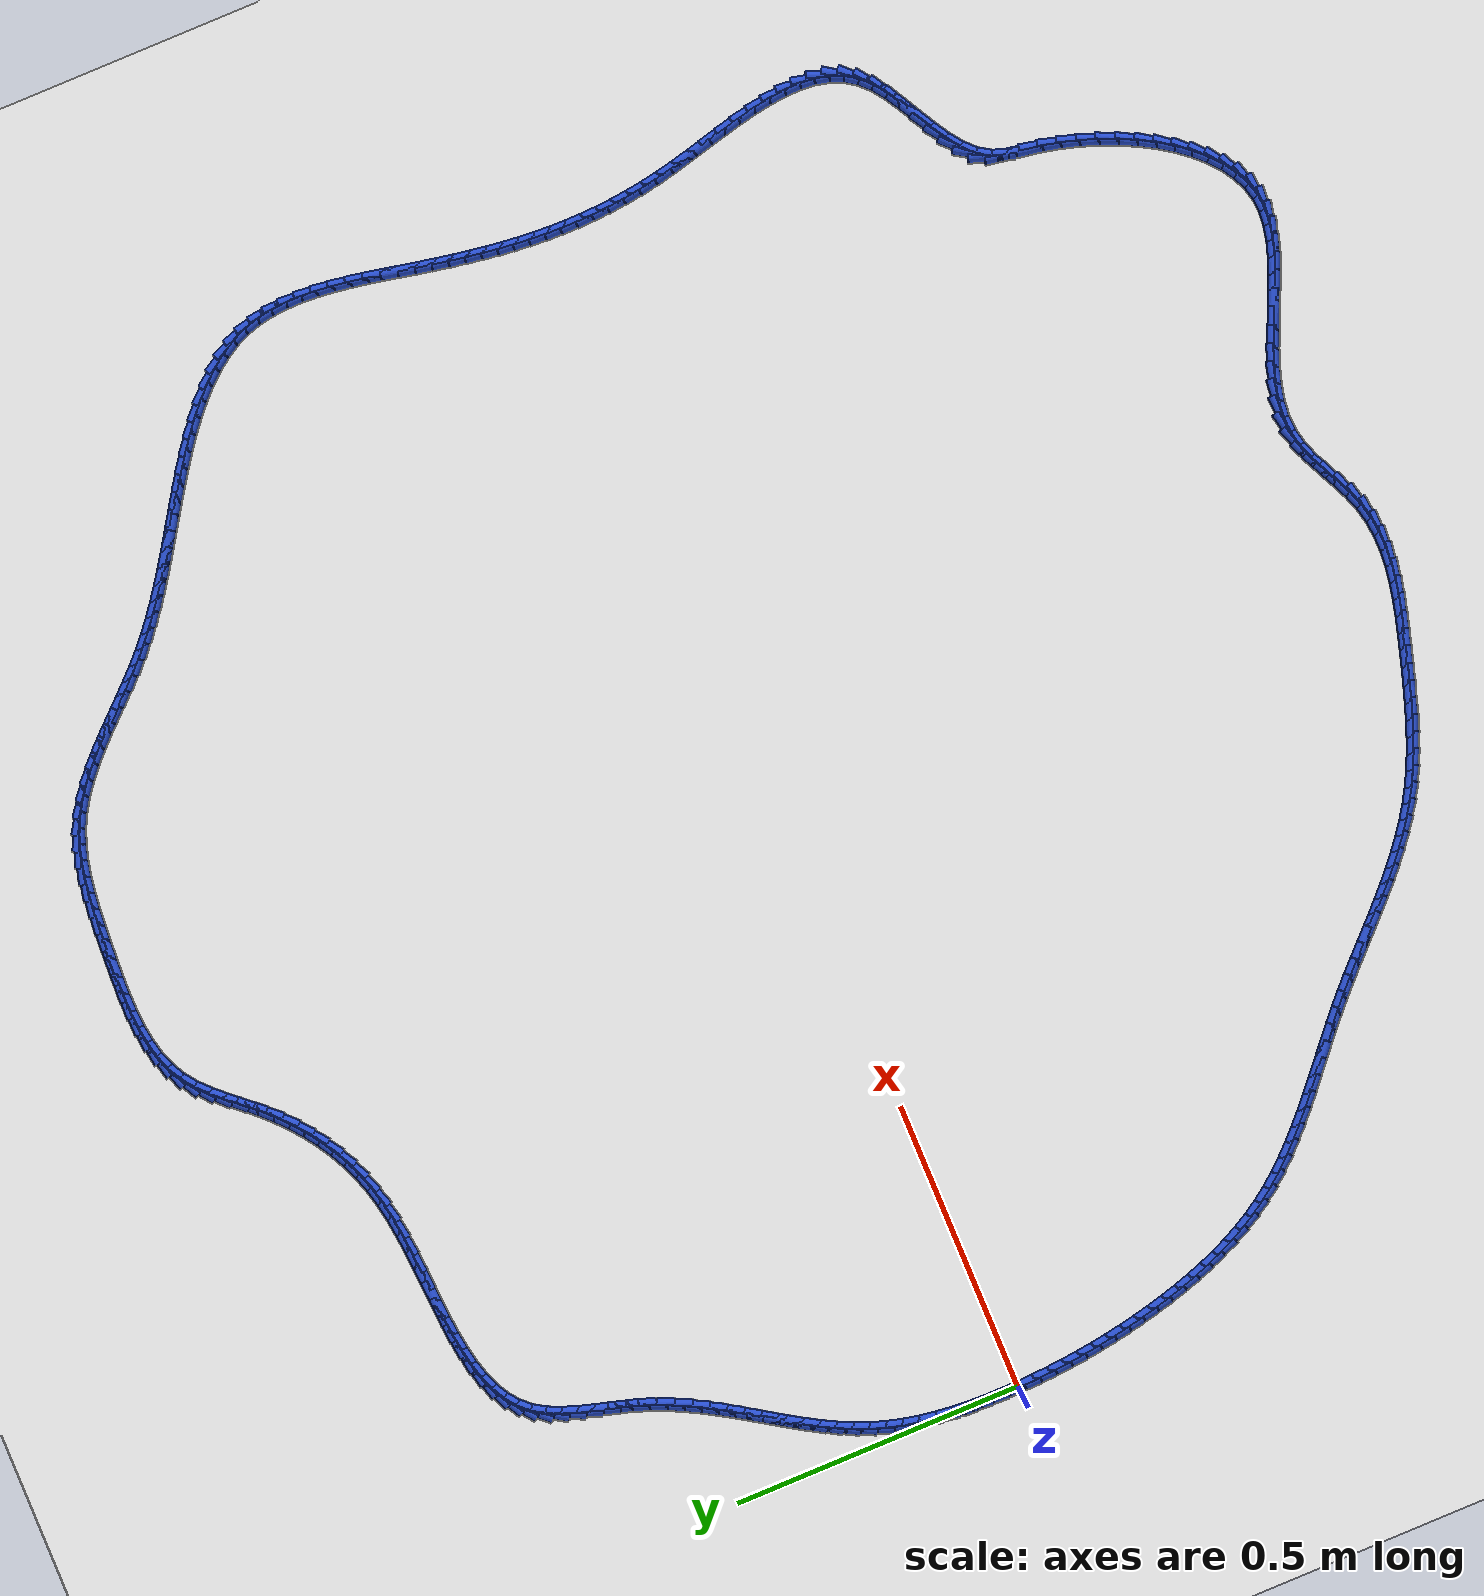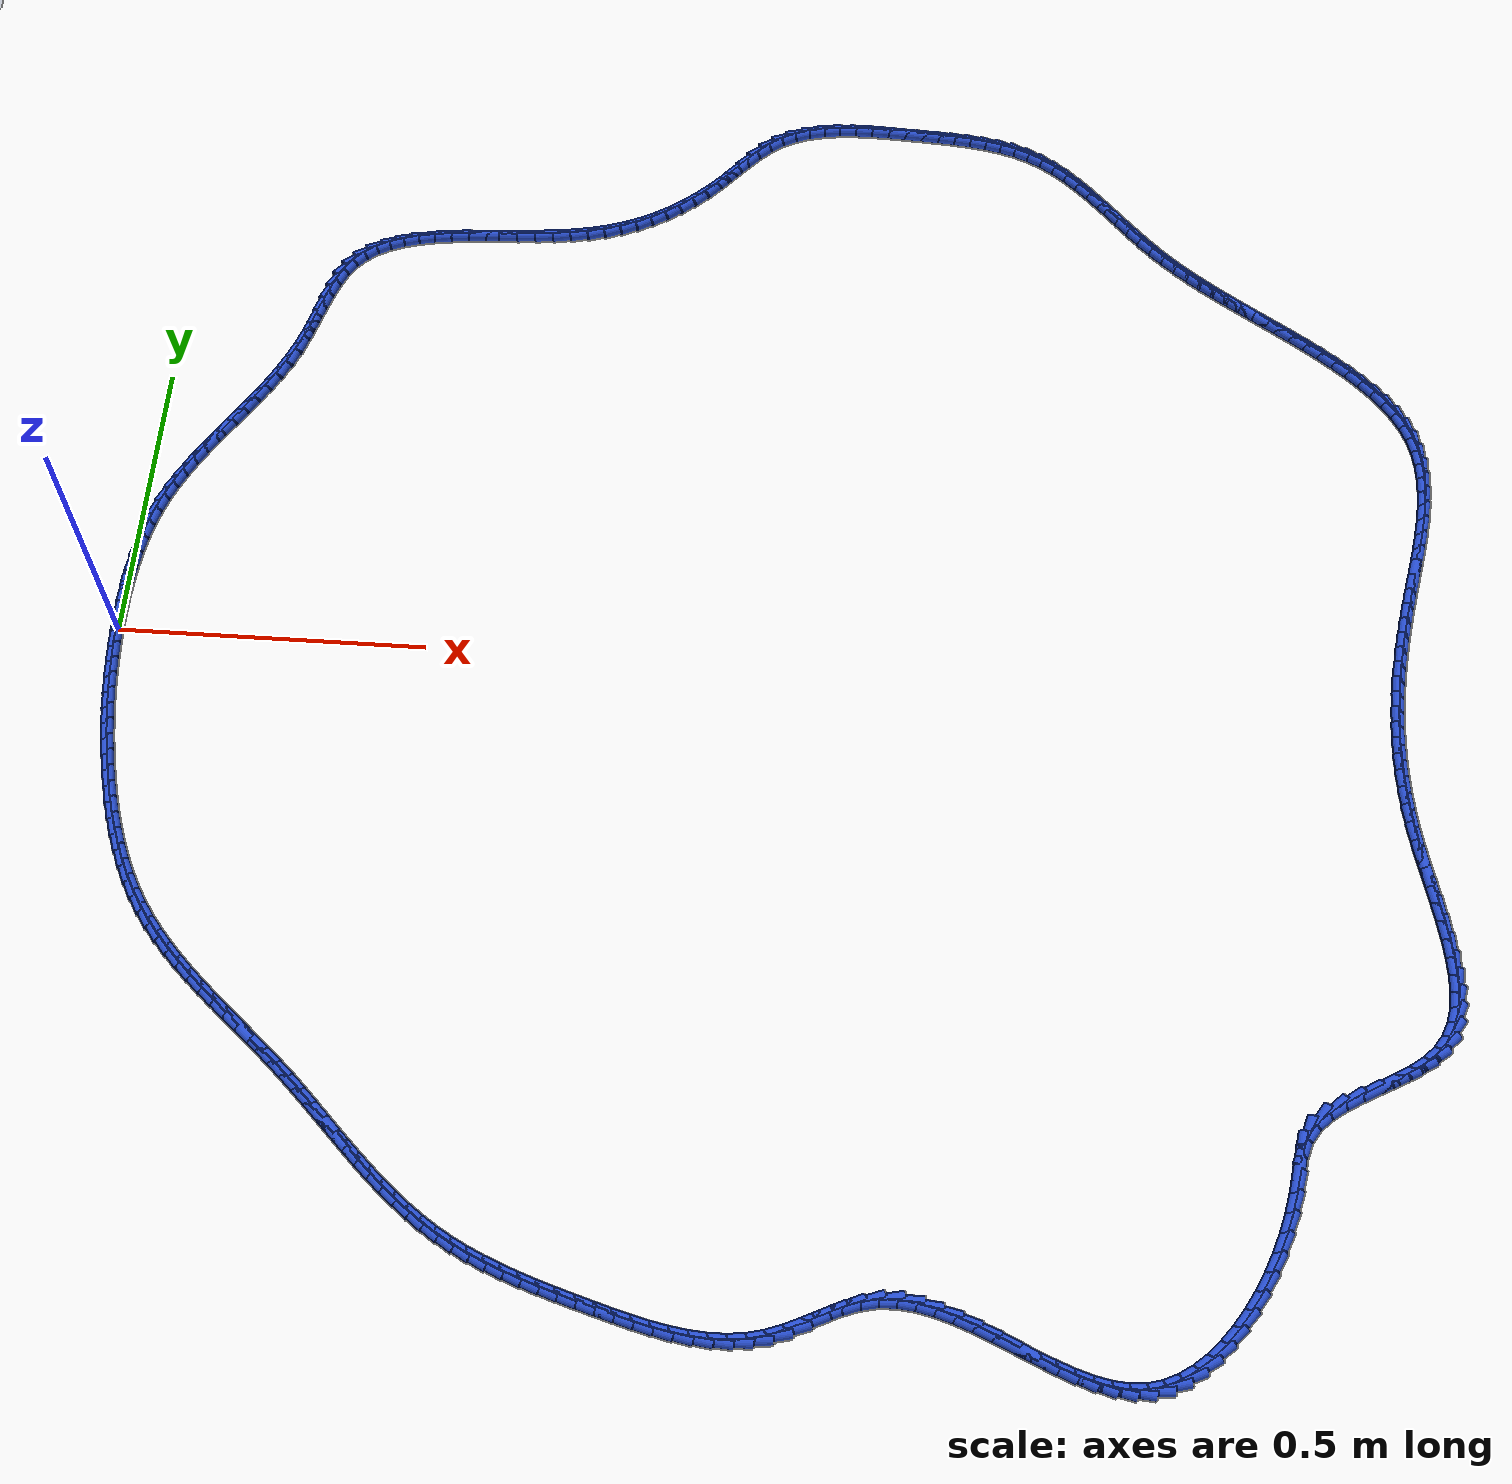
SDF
<sdf version="1.6">
 <world name="default">
  <light name="sun" type="directional">
   <pose>0 0 10 0 -0 0</pose>
   <diffuse>0.8 0.8 0.8 1</diffuse>
   <specular>0.2 0.2 0.2 1</specular>
   <attenuation>
    <range>1000</range>
    <constant>0.9</constant>
    <linear>0.01</linear>
    <quadratic>0.001</quadratic>
   </attenuation>
   <direction>-0.5 0.1 -0.9</direction>
  </light>
  <model name="ground_plane">
   <static>1</static>
   <link name="link">
    <collision name="collision">
     <geometry><plane><normal>0 0 1</normal><size>100 100</size></plane></geometry>
     <surface><friction><ode><mu>100</mu><mu2>50</mu2></ode></friction></surface>
    </collision>
    <visual name="visual">
     <cast_shadows>0</cast_shadows>
     <geometry><plane><normal>0 0 1</normal><size>100 100</size></plane></geometry>
     <material>
      <script><uri>file://media/materials/scripts/gazebo.material</uri><name>Gazebo/WhiteGlow</name></script>
     </material>
    </visual>
   </link>
  </model>
  <gravity>0 0 -9.8</gravity>
  <magnetic_field>6e-06 2.3e-05 -4.2e-05</magnetic_field>
  <atmosphere type="adiabatic"/>
  <physics name="default_physics" default="0" type="ode">
   <max_step_size>0.001</max_step_size>
   <real_time_factor>1</real_time_factor>
   <real_time_update_rate>1000</real_time_update_rate>
  </physics>
  <scene><ambient>0.4 0.4 0.4 1</ambient><background>0.7 0.7 0.7 1</background><shadows>1</shadows></scene>
  <spherical_coordinates>
   <surface_model>EARTH_WGS84</surface_model>
   <latitude_deg>0</latitude_deg>
   <longitude_deg>0</longitude_deg>
   <elevation>0</elevation>
   <heading_deg>0</heading_deg>
  </spherical_coordinates>
  <model name="line">
   <link name="link_0">
    <pose>-6.938893903907228e-18 1.3877787807814457e-17 0.01 0 1.57 -1.5556264932809063</pose>
    <collision name="collision">
     <geometry><cylinder><radius>0.01</radius><length>0.08</length></cylinder></geometry>
    </collision>
    <visual name="visual">
     <material>
      <script><name>Gazebo/Blue</name><uri>file://media/materials/scripts/gazebo.material</uri></script>
     </material>
     <geometry><cylinder><radius>0.01</radius><length>0.08</length></cylinder></geometry>
    </visual>
   </link>
   <link name="link_1">
    <pose>-0.0004328668530601711 0.028532524620181948 0.01 0 1.57 1.5608192259742957</pose>
    <collision name="collision">
     <geometry><cylinder><radius>0.01</radius><length>0.08</length></cylinder></geometry>
    </collision>
    <visual name="visual">
     <material>
      <script><name>Gazebo/Blue</name><uri>file://media/materials/scripts/gazebo.material</uri></script>
     </material>
     <geometry><cylinder><radius>0.01</radius><length>0.08</length></cylinder></geometry>
    </visual>
   </link>
   <link name="link_2">
    <pose>-0.00014729697651953791 0.05715410579512215 0.01 0 1.57 1.5314724917271418</pose>
    <collision name="collision">
     <geometry><cylinder><radius>0.01</radius><length>0.08</length></cylinder></geometry>
    </collision>
    <visual name="visual">
     <material>
      <script><name>Gazebo/Blue</name><uri>file://media/materials/scripts/gazebo.material</uri></script>
     </material>
     <geometry><cylinder><radius>0.01</radius><length>0.08</length></cylinder></geometry>
    </visual>
   </link>
   <link name="link_3">
    <pose>0.000977937755280431 0.08575392731722464 0.01 0 1.57 1.4976454005490114</pose>
    <collision name="collision">
     <geometry><cylinder><radius>0.01</radius><length>0.08</length></cylinder></geometry>
    </collision>
    <visual name="visual">
     <material>
      <script><name>Gazebo/Blue</name><uri>file://media/materials/scripts/gazebo.material</uri></script>
     </material>
     <geometry><cylinder><radius>0.01</radius><length>0.08</length></cylinder></geometry>
    </visual>
   </link>
   <link name="link_4">
    <pose>0.0030640654679982694 0.11422117297889346 0.01 0 1.57 1.4590100040305665</pose>
    <collision name="collision">
     <geometry><cylinder><radius>0.01</radius><length>0.08</length></cylinder></geometry>
    </collision>
    <visual name="visual">
     <material>
      <script><name>Gazebo/Blue</name><uri>file://media/materials/scripts/gazebo.material</uri></script>
     </material>
     <geometry><cylinder><radius>0.01</radius><length>0.08</length></cylinder></geometry>
    </visual>
   </link>
   <link name="link_5">
    <pose>0.006232314287292515 0.1424450265725326 0.01 0 1.57 1.4152053866295176</pose>
    <collision name="collision">
     <geometry><cylinder><radius>0.01</radius><length>0.08</length></cylinder></geometry>
    </collision>
    <visual name="visual">
     <material>
      <script><name>Gazebo/Blue</name><uri>file://media/materials/scripts/gazebo.material</uri></script>
     </material>
     <geometry><cylinder><radius>0.01</radius><length>0.08</length></cylinder></geometry>
    </visual>
   </link>
   <link name="link_6">
    <pose>0.010603912338821696 0.170314671890546 0.01 0 1.57 1.3658598389447063</pose>
    <collision name="collision">
     <geometry><cylinder><radius>0.01</radius><length>0.08</length></cylinder></geometry>
    </collision>
    <visual name="visual">
     <material>
      <script><name>Gazebo/Blue</name><uri>file://media/materials/scripts/gazebo.material</uri></script>
     </material>
     <geometry><cylinder><radius>0.01</radius><length>0.08</length></cylinder></geometry>
    </visual>
   </link>
   <link name="link_7">
    <pose>0.016300087748244353 0.19771929272533761 0.01 0 1.57 1.3106241144694624</pose>
    <collision name="collision">
     <geometry><cylinder><radius>0.01</radius><length>0.08</length></cylinder></geometry>
    </collision>
    <visual name="visual">
     <material>
      <script><name>Gazebo/Blue</name><uri>file://media/materials/scripts/gazebo.material</uri></script>
     </material>
     <geometry><cylinder><radius>0.01</radius><length>0.08</length></cylinder></geometry>
    </visual>
   </link>
   <link name="link_8">
    <pose>0.023442068641219026 0.22454807286931164 0.01 0 1.57 1.2492200318941575</pose>
    <collision name="collision">
     <geometry><cylinder><radius>0.01</radius><length>0.08</length></cylinder></geometry>
    </collision>
    <visual name="visual">
     <material>
      <script><name>Gazebo/Blue</name><uri>file://media/materials/scripts/gazebo.material</uri></script>
     </material>
     <geometry><cylinder><radius>0.01</radius><length>0.08</length></cylinder></geometry>
    </visual>
   </link>
   <link name="link_9">
    <pose>0.03215105480468282 0.2506902155332027 0.01 0 1.57 1.184782731723996</pose>
    <collision name="collision">
     <geometry><cylinder><radius>0.01</radius><length>0.08</length></cylinder></geometry>
    </collision>
    <visual name="visual">
     <material>
      <script><name>Gazebo/Blue</name><uri>file://media/materials/scripts/gazebo.material</uri></script>
     </material>
     <geometry><cylinder><radius>0.01</radius><length>0.08</length></cylinder></geometry>
    </visual>
   </link>
   <link name="link_10">
    <pose>0.042472345266808854 0.27608693283851216 0.01 0 1.57 1.1280689015237728</pose>
    <collision name="collision">
     <geometry><cylinder><radius>0.01</radius><length>0.08</length></cylinder></geometry>
    </collision>
    <visual name="visual">
     <material>
      <script><name>Gazebo/Blue</name><uri>file://media/materials/scripts/gazebo.material</uri></script>
     </material>
     <geometry><cylinder><radius>0.01</radius><length>0.08</length></cylinder></geometry>
    </visual>
   </link>
   <link name="link_11">
    <pose>0.05421032883693355 0.30084451401899054 0.01 0 1.57 1.0816708709063352</pose>
    <collision name="collision">
     <geometry><cylinder><radius>0.01</radius><length>0.08</length></cylinder></geometry>
    </collision>
    <visual name="visual">
     <material>
      <script><name>Gazebo/Blue</name><uri>file://media/materials/scripts/gazebo.material</uri></script>
     </material>
     <geometry><cylinder><radius>0.01</radius><length>0.08</length></cylinder></geometry>
    </visual>
   </link>
   <link name="link_12">
    <pose>0.06712170715413104 0.3251019246323582 0.01 0 1.57 1.045786533843919</pose>
    <collision name="collision">
     <geometry><cylinder><radius>0.01</radius><length>0.08</length></cylinder></geometry>
    </collision>
    <visual name="visual">
     <material>
      <script><name>Gazebo/Blue</name><uri>file://media/materials/scripts/gazebo.material</uri></script>
     </material>
     <geometry><cylinder><radius>0.01</radius><length>0.08</length></cylinder></geometry>
    </visual>
   </link>
   <link name="link_13">
    <pose>0.08096318185747539 0.34899813023633497 0.01 0 1.57 1.0203776618018388</pose>
    <collision name="collision">
     <geometry><cylinder><radius>0.01</radius><length>0.08</length></cylinder></geometry>
    </collision>
    <visual name="visual">
     <material>
      <script><name>Gazebo/Blue</name><uri>file://media/materials/scripts/gazebo.material</uri></script>
     </material>
     <geometry><cylinder><radius>0.01</radius><length>0.08</length></cylinder></geometry>
    </visual>
   </link>
   <link name="link_14">
    <pose>0.09549145458604062 0.3726720963886408 0.01 0 1.57 1.0052895886531499</pose>
    <collision name="collision">
     <geometry><cylinder><radius>0.01</radius><length>0.08</length></cylinder></geometry>
    </collision>
    <visual name="visual">
     <material>
      <script><name>Gazebo/Blue</name><uri>file://media/materials/scripts/gazebo.material</uri></script>
     </material>
     <geometry><cylinder><radius>0.01</radius><length>0.08</length></cylinder></geometry>
    </visual>
   </link>
   <link name="link_15">
    <pose>0.11046322697890087 0.3962627886469958 0.01 0 1.57 1.0003352925455387</pose>
    <collision name="collision">
     <geometry><cylinder><radius>0.01</radius><length>0.08</length></cylinder></geometry>
    </collision>
    <visual name="visual">
     <material>
      <script><name>Gazebo/Blue</name><uri>file://media/materials/scripts/gazebo.material</uri></script>
     </material>
     <geometry><cylinder><radius>0.01</radius><length>0.08</length></cylinder></geometry>
    </visual>
   </link>
   <link name="link_16">
    <pose>0.1256352006751302 0.41990917256912 0.01 0 1.57 1.0053427853454664</pose>
    <collision name="collision">
     <geometry><cylinder><radius>0.01</radius><length>0.08</length></cylinder></geometry>
    </collision>
    <visual name="visual">
     <material>
      <script><name>Gazebo/Blue</name><uri>file://media/materials/scripts/gazebo.material</uri></script>
     </material>
     <geometry><cylinder><radius>0.01</radius><length>0.08</length></cylinder></geometry>
    </visual>
   </link>
   <link name="link_17">
    <pose>0.14076407731380272 0.4437502137127334 0.01 0 1.57 1.0201691608739643</pose>
    <collision name="collision">
     <geometry><cylinder><radius>0.01</radius><length>0.08</length></cylinder></geometry>
    </collision>
    <visual name="visual">
     <material>
      <script><name>Gazebo/Blue</name><uri>file://media/materials/scripts/gazebo.material</uri></script>
     </material>
     <geometry><cylinder><radius>0.01</radius><length>0.08</length></cylinder></geometry>
    </visual>
   </link>
   <link name="link_18">
    <pose>0.15560655853399247 0.467924877635556 0.01 0 1.57 1.0446850118273008</pose>
    <collision name="collision">
     <geometry><cylinder><radius>0.01</radius><length>0.08</length></cylinder></geometry>
    </collision>
    <visual name="visual">
     <material>
      <script><name>Gazebo/Blue</name><uri>file://media/materials/scripts/gazebo.material</uri></script>
     </material>
     <geometry><cylinder><radius>0.01</radius><length>0.08</length></cylinder></geometry>
    </visual>
   </link>
   <link name="link_19">
    <pose>0.16991934597477346 0.4925721298953077 0.01 0 1.57 1.0787321085161339</pose>
    <collision name="collision">
     <geometry><cylinder><radius>0.01</radius><length>0.08</length></cylinder></geometry>
    </collision>
    <visual name="visual">
     <material>
      <script><name>Gazebo/Blue</name><uri>file://media/materials/scripts/gazebo.material</uri></script>
     </material>
     <geometry><cylinder><radius>0.01</radius><length>0.08</length></cylinder></geometry>
    </visual>
   </link>
   <link name="link_20">
    <pose>0.18345914127521995 0.5178309360497088 0.01 0 1.57 1.1220574963081096</pose>
    <collision name="collision">
     <geometry><cylinder><radius>0.01</radius><length>0.08</length></cylinder></geometry>
    </collision>
    <visual name="visual">
     <material>
      <script><name>Gazebo/Blue</name><uri>file://media/materials/scripts/gazebo.material</uri></script>
     </material>
     <geometry><cylinder><radius>0.01</radius><length>0.08</length></cylinder></geometry>
    </visual>
   </link>
   <link name="link_21">
    <pose>0.19598264607440585 0.543840261656479 0.01 0 1.57 1.1742301397448864</pose>
    <collision name="collision">
     <geometry><cylinder><radius>0.01</radius><length>0.08</length></cylinder></geometry>
    </collision>
    <visual name="visual">
     <material>
      <script><name>Gazebo/Blue</name><uri>file://media/materials/scripts/gazebo.material</uri></script>
     </material>
     <geometry><cylinder><radius>0.01</radius><length>0.08</length></cylinder></geometry>
    </visual>
   </link>
   <link name="link_22">
    <pose>0.2072465620114053 0.5707390722733385 0.01 0 1.57 1.233449453714175</pose>
    <collision name="collision">
     <geometry><cylinder><radius>0.01</radius><length>0.08</length></cylinder></geometry>
    </collision>
    <visual name="visual">
     <material>
      <script><name>Gazebo/Blue</name><uri>file://media/materials/scripts/gazebo.material</uri></script>
     </material>
     <geometry><cylinder><radius>0.01</radius><length>0.08</length></cylinder></geometry>
    </visual>
   </link>
   <link name="link_23">
    <pose>0.2170339715433079 0.5986429421226758 0.01 0 1.57 1.279112003295565</pose>
    <collision name="collision">
     <geometry><cylinder><radius>0.01</radius><length>0.08</length></cylinder></geometry>
    </collision>
    <visual name="visual">
     <material>
      <script><name>Gazebo/Blue</name><uri>file://media/materials/scripts/gazebo.material</uri></script>
     </material>
     <geometry><cylinder><radius>0.01</radius><length>0.08</length></cylinder></geometry>
    </visual>
   </link>
   <link name="link_24">
    <pose>0.22561804754991704 0.6272328922066633 0.01 0 1.57 1.2949888499130187</pose>
    <collision name="collision">
     <geometry><cylinder><radius>0.01</radius><length>0.08</length></cylinder></geometry>
    </collision>
    <visual name="visual">
     <material>
      <script><name>Gazebo/Blue</name><uri>file://media/materials/scripts/gazebo.material</uri></script>
     </material>
     <geometry><cylinder><radius>0.01</radius><length>0.08</length></cylinder></geometry>
    </visual>
   </link>
   <link name="link_25">
    <pose>0.233704855109308 0.6558061068107246 0.01 0 1.57 1.280712569614745</pose>
    <collision name="collision">
     <geometry><cylinder><radius>0.01</radius><length>0.08</length></cylinder></geometry>
    </collision>
    <visual name="visual">
     <material>
      <script><name>Gazebo/Blue</name><uri>file://media/materials/scripts/gazebo.material</uri></script>
     </material>
     <geometry><cylinder><radius>0.01</radius><length>0.08</length></cylinder></geometry>
    </visual>
   </link>
   <link name="link_26">
    <pose>0.24201534521463663 0.6836465711818305 0.01 0 1.57 1.2335130614606669</pose>
    <collision name="collision">
     <geometry><cylinder><radius>0.01</radius><length>0.08</length></cylinder></geometry>
    </collision>
    <visual name="visual">
     <material>
      <script><name>Gazebo/Blue</name><uri>file://media/materials/scripts/gazebo.material</uri></script>
     </material>
     <geometry><cylinder><radius>0.01</radius><length>0.08</length></cylinder></geometry>
    </visual>
   </link>
   <link name="link_27">
    <pose>0.2512704688590588 0.7100382705669519 0.01 0 1.57 1.1473043243663825</pose>
    <collision name="collision">
     <geometry><cylinder><radius>0.01</radius><length>0.08</length></cylinder></geometry>
    </collision>
    <visual name="visual">
     <material>
      <script><name>Gazebo/Blue</name><uri>file://media/materials/scripts/gazebo.material</uri></script>
     </material>
     <geometry><cylinder><radius>0.01</radius><length>0.08</length></cylinder></geometry>
    </visual>
   </link>
   <link name="link_28">
    <pose>0.2621911770357306 0.7342651902130609 0.01 0 1.57 1.0133469281932523</pose>
    <collision name="collision">
     <geometry><cylinder><radius>0.01</radius><length>0.08</length></cylinder></geometry>
    </collision>
    <visual name="visual">
     <material>
      <script><name>Gazebo/Blue</name><uri>file://media/materials/scripts/gazebo.material</uri></script>
     </material>
     <geometry><cylinder><radius>0.01</radius><length>0.08</length></cylinder></geometry>
    </visual>
   </link>
   <link name="link_29">
    <pose>0.27549840537468545 0.7556113318411133 0.01 0 1.57 0.8359203690613224</pose>
    <collision name="collision">
     <geometry><cylinder><radius>0.01</radius><length>0.08</length></cylinder></geometry>
    </collision>
    <visual name="visual">
     <material>
      <script><name>Gazebo/Blue</name><uri>file://media/materials/scripts/gazebo.material</uri></script>
     </material>
     <geometry><cylinder><radius>0.01</radius><length>0.08</length></cylinder></geometry>
    </visual>
   </link>
   <link name="link_30">
    <pose>0.2917231918221372 0.7735643258024689 0.01 0 1.57 0.6601715932691534</pose>
    <collision name="collision">
     <geometry><cylinder><radius>0.01</radius><length>0.08</length></cylinder></geometry>
    </collision>
    <visual name="visual">
     <material>
      <script><name>Gazebo/Blue</name><uri>file://media/materials/scripts/gazebo.material</uri></script>
     </material>
     <geometry><cylinder><radius>0.01</radius><length>0.08</length></cylinder></geometry>
    </visual>
   </link>
   <link name="link_31">
    <pose>0.31073310770774487 0.7883232423972535 0.01 0 1.57 0.5058495002809777</pose>
    <collision name="collision">
     <geometry><cylinder><radius>0.01</radius><length>0.08</length></cylinder></geometry>
    </collision>
    <visual name="visual">
     <material>
      <script><name>Gazebo/Blue</name><uri>file://media/materials/scripts/gazebo.material</uri></script>
     </material>
     <geometry><cylinder><radius>0.01</radius><length>0.08</length></cylinder></geometry>
    </visual>
   </link>
   <link name="link_32">
    <pose>0.33225091421048747 0.8002424328750943 0.01 0 1.57 0.37812400585318784</pose>
    <collision name="collision">
     <geometry><cylinder><radius>0.01</radius><length>0.08</length></cylinder></geometry>
    </collision>
    <visual name="visual">
     <material>
      <script><name>Gazebo/Blue</name><uri>file://media/materials/scripts/gazebo.material</uri></script>
     </material>
     <geometry><cylinder><radius>0.01</radius><length>0.08</length></cylinder></geometry>
    </visual>
   </link>
   <link name="link_33">
    <pose>0.355999372509344 0.8096762484856186 0.01 0 1.57 0.2768386250746045</pose>
    <collision name="collision">
     <geometry><cylinder><radius>0.01</radius><length>0.08</length></cylinder></geometry>
    </collision>
    <visual name="visual">
     <material>
      <script><name>Gazebo/Blue</name><uri>file://media/materials/scripts/gazebo.material</uri></script>
     </material>
     <geometry><cylinder><radius>0.01</radius><length>0.08</length></cylinder></geometry>
    </visual>
   </link>
   <link name="link_34">
    <pose>0.3817012437832932 0.8169790404784529 0.01 0 1.57 0.19916889863321954</pose>
    <collision name="collision">
     <geometry><cylinder><radius>0.01</radius><length>0.08</length></cylinder></geometry>
    </collision>
    <visual name="visual">
     <material>
      <script><name>Gazebo/Blue</name><uri>file://media/materials/scripts/gazebo.material</uri></script>
     </material>
     <geometry><cylinder><radius>0.01</radius><length>0.08</length></cylinder></geometry>
    </visual>
   </link>
   <link name="link_35">
    <pose>0.4090792892113141 0.8225051601032244 0.01 0 1.57 0.14165189277365298</pose>
    <collision name="collision">
     <geometry><cylinder><radius>0.01</radius><length>0.08</length></cylinder></geometry>
    </collision>
    <visual name="visual">
     <material>
      <script><name>Gazebo/Blue</name><uri>file://media/materials/scripts/gazebo.material</uri></script>
     </material>
     <geometry><cylinder><radius>0.01</radius><length>0.08</length></cylinder></geometry>
    </visual>
   </link>
   <link name="link_36">
    <pose>0.4378562699723855 0.8266089586095599 0.01 0 1.57 0.10119042187298158</pose>
    <collision name="collision">
     <geometry><cylinder><radius>0.01</radius><length>0.08</length></cylinder></geometry>
    </collision>
    <visual name="visual">
     <material>
      <script><name>Gazebo/Blue</name><uri>file://media/materials/scripts/gazebo.material</uri></script>
     </material>
     <geometry><cylinder><radius>0.01</radius><length>0.08</length></cylinder></geometry>
    </visual>
   </link>
   <link name="link_37">
    <pose>0.46775494724548655 0.8296447872470865 0.01 0 1.57 0.07539271746639593</pose>
    <collision name="collision">
     <geometry><cylinder><radius>0.01</radius><length>0.08</length></cylinder></geometry>
    </collision>
    <visual name="visual">
     <material>
      <script><name>Gazebo/Blue</name><uri>file://media/materials/scripts/gazebo.material</uri></script>
     </material>
     <geometry><cylinder><radius>0.01</radius><length>0.08</length></cylinder></geometry>
    </visual>
   </link>
   <link name="link_38">
    <pose>0.4984980822095961 0.831966997265431 0.01 0 1.57 0.06261114056649036</pose>
    <collision name="collision">
     <geometry><cylinder><radius>0.01</radius><length>0.08</length></cylinder></geometry>
    </collision>
    <visual name="visual">
     <material>
      <script><name>Gazebo/Blue</name><uri>file://media/materials/scripts/gazebo.material</uri></script>
     </material>
     <geometry><cylinder><radius>0.01</radius><length>0.08</length></cylinder></geometry>
    </visual>
   </link>
   <link name="link_39">
    <pose>0.5298084360436934 0.8339299399142206 0.01 0 1.57 0.061883094828041746</pose>
    <collision name="collision">
     <geometry><cylinder><radius>0.01</radius><length>0.08</length></cylinder></geometry>
    </collision>
    <visual name="visual">
     <material>
      <script><name>Gazebo/Blue</name><uri>file://media/materials/scripts/gazebo.material</uri></script>
     </material>
     <geometry><cylinder><radius>0.01</radius><length>0.08</length></cylinder></geometry>
    </visual>
   </link>
   <link name="link_40">
    <pose>0.5614087699267569 0.835887966443082 0.01 0 1.57 0.07286152703590727</pose>
    <collision name="collision">
     <geometry><cylinder><radius>0.01</radius><length>0.08</length></cylinder></geometry>
    </collision>
    <visual name="visual">
     <material>
      <script><name>Gazebo/Blue</name><uri>file://media/materials/scripts/gazebo.material</uri></script>
     </material>
     <geometry><cylinder><radius>0.01</radius><length>0.08</length></cylinder></geometry>
    </visual>
   </link>
   <link name="link_41">
    <pose>0.5930218450377658 0.8381954281016423 0.01 0 1.57 0.09576311542898577</pose>
    <collision name="collision">
     <geometry><cylinder><radius>0.01</radius><length>0.08</length></cylinder></geometry>
    </collision>
    <visual name="visual">
     <material>
      <script><name>Gazebo/Blue</name><uri>file://media/materials/scripts/gazebo.material</uri></script>
     </material>
     <geometry><cylinder><radius>0.01</radius><length>0.08</length></cylinder></geometry>
    </visual>
   </link>
   <link name="link_42">
    <pose>0.6243704225556992 0.8412066761395286 0.01 0 1.57 0.1313332283863889</pose>
    <collision name="collision">
     <geometry><cylinder><radius>0.01</radius><length>0.08</length></cylinder></geometry>
    </collision>
    <visual name="visual">
     <material>
      <script><name>Gazebo/Blue</name><uri>file://media/materials/scripts/gazebo.material</uri></script>
     </material>
     <geometry><cylinder><radius>0.01</radius><length>0.08</length></cylinder></geometry>
    </visual>
   </link>
   <link name="link_43">
    <pose>0.6551772636595357 0.8452760618063675 0.01 0 1.57 0.18080672545606608</pose>
    <collision name="collision">
     <geometry><cylinder><radius>0.01</radius><length>0.08</length></cylinder></geometry>
    </collision>
    <visual name="visual">
     <material>
      <script><name>Gazebo/Blue</name><uri>file://media/materials/scripts/gazebo.material</uri></script>
     </material>
     <geometry><cylinder><radius>0.01</radius><length>0.08</length></cylinder></geometry>
    </visual>
   </link>
   <link name="link_44">
    <pose>0.6851651295282543 0.8507579363517863 0.01 0 1.57 0.2457385323780613</pose>
    <collision name="collision">
     <geometry><cylinder><radius>0.01</radius><length>0.08</length></cylinder></geometry>
    </collision>
    <visual name="visual">
     <material>
      <script><name>Gazebo/Blue</name><uri>file://media/materials/scripts/gazebo.material</uri></script>
     </material>
     <geometry><cylinder><radius>0.01</radius><length>0.08</length></cylinder></geometry>
    </visual>
   </link>
   <link name="link_45">
    <pose>0.7140582869654187 0.858004557358594 0.01 0 1.57 0.3215207651898742</pose>
    <collision name="collision">
     <geometry><cylinder><radius>0.01</radius><length>0.08</length></cylinder></geometry>
    </collision>
    <visual name="visual">
     <material>
      <script><name>Gazebo/Blue</name><uri>file://media/materials/scripts/gazebo.material</uri></script>
     </material>
     <geometry><cylinder><radius>0.01</radius><length>0.08</length></cylinder></geometry>
    </visual>
   </link>
   <link name="link_46">
    <pose>0.7416949551399105 0.8672097243925659 0.01 0 1.57 0.3975840211138584</pose>
    <collision name="collision">
     <geometry><cylinder><radius>0.01</radius><length>0.08</length></cylinder></geometry>
    </collision>
    <visual name="visual">
     <material>
      <script><name>Gazebo/Blue</name><uri>file://media/materials/scripts/gazebo.material</uri></script>
     </material>
     <geometry><cylinder><radius>0.01</radius><length>0.08</length></cylinder></geometry>
    </visual>
   </link>
   <link name="link_47">
    <pose>0.7681050899315821 0.8783006149188444 0.01 0 1.57 0.4719273806635027</pose>
    <collision name="collision">
     <geometry><cylinder><radius>0.01</radius><length>0.08</length></cylinder></geometry>
    </collision>
    <visual name="visual">
     <material>
      <script><name>Gazebo/Blue</name><uri>file://media/materials/scripts/gazebo.material</uri></script>
     </material>
     <geometry><cylinder><radius>0.01</radius><length>0.08</length></cylinder></geometry>
    </visual>
   </link>
   <link name="link_48">
    <pose>0.7933370426414579 0.8911788263985657 0.01 0 1.57 0.5436426621191703</pose>
    <collision name="collision">
     <geometry><cylinder><radius>0.01</radius><length>0.08</length></cylinder></geometry>
    </collision>
    <visual name="visual">
     <material>
      <script><name>Gazebo/Blue</name><uri>file://media/materials/scripts/gazebo.material</uri></script>
     </material>
     <geometry><cylinder><radius>0.01</radius><length>0.08</length></cylinder></geometry>
    </visual>
   </link>
   <link name="link_49">
    <pose>0.8174391645705625 0.9057459562928657 0.01 0 1.57 0.6119841869753357</pose>
    <collision name="collision">
     <geometry><cylinder><radius>0.01</radius><length>0.08</length></cylinder></geometry>
    </collision>
    <visual name="visual">
     <material>
      <script><name>Gazebo/Blue</name><uri>file://media/materials/scripts/gazebo.material</uri></script>
     </material>
     <geometry><cylinder><radius>0.01</radius><length>0.08</length></cylinder></geometry>
    </visual>
   </link>
   <link name="link_50">
    <pose>0.8404598070199204 0.9219036020628806 0.01 0 1.57 0.6763956657879273</pose>
    <collision name="collision">
     <geometry><cylinder><radius>0.01</radius><length>0.08</length></cylinder></geometry>
    </collision>
    <visual name="visual">
     <material>
      <script><name>Gazebo/Blue</name><uri>file://media/materials/scripts/gazebo.material</uri></script>
     </material>
     <geometry><cylinder><radius>0.01</radius><length>0.08</length></cylinder></geometry>
    </visual>
   </link>
   <link name="link_51">
    <pose>0.8624473212905558 0.9395533611697462 0.01 0 1.57 0.7365119746632101</pose>
    <collision name="collision">
     <geometry><cylinder><radius>0.01</radius><length>0.08</length></cylinder></geometry>
    </collision>
    <visual name="visual">
     <material>
      <script><name>Gazebo/Blue</name><uri>file://media/materials/scripts/gazebo.material</uri></script>
     </material>
     <geometry><cylinder><radius>0.01</radius><length>0.08</length></cylinder></geometry>
    </visual>
   </link>
   <link name="link_52">
    <pose>0.883450058683493 0.9585968310745987 0.01 0 1.57 0.7921414281198801</pose>
    <collision name="collision">
     <geometry><cylinder><radius>0.01</radius><length>0.08</length></cylinder></geometry>
    </collision>
    <visual name="visual">
     <material>
      <script><name>Gazebo/Blue</name><uri>file://media/materials/scripts/gazebo.material</uri></script>
     </material>
     <geometry><cylinder><radius>0.01</radius><length>0.08</length></cylinder></geometry>
    </visual>
   </link>
   <link name="link_53">
    <pose>0.9035163704997567 0.978935609238574 0.01 0 1.57 0.8401408423497367</pose>
    <collision name="collision">
     <geometry><cylinder><radius>0.01</radius><length>0.08</length></cylinder></geometry>
    </collision>
    <visual name="visual">
     <material>
      <script><name>Gazebo/Blue</name><uri>file://media/materials/scripts/gazebo.material</uri></script>
     </material>
     <geometry><cylinder><radius>0.01</radius><length>0.08</length></cylinder></geometry>
    </visual>
   </link>
   <link name="link_54">
    <pose>0.9227425897094619 1.000391080456706 0.01 0 1.57 0.8572560529921394</pose>
    <collision name="collision">
     <geometry><cylinder><radius>0.01</radius><length>0.08</length></cylinder></geometry>
    </collision>
    <visual name="visual">
     <material>
      <script><name>Gazebo/Blue</name><uri>file://media/materials/scripts/gazebo.material</uri></script>
     </material>
     <geometry><cylinder><radius>0.01</radius><length>0.08</length></cylinder></geometry>
    </visual>
   </link>
   <link name="link_55">
    <pose>0.9415943281046684 1.0221672929576888 0.01 0 1.57 0.8327134173107609</pose>
    <collision name="collision">
     <geometry><cylinder><radius>0.01</radius><length>0.08</length></cylinder></geometry>
    </collision>
    <visual name="visual">
     <material>
      <script><name>Gazebo/Blue</name><uri>file://media/materials/scripts/gazebo.material</uri></script>
     </material>
     <geometry><cylinder><radius>0.01</radius><length>0.08</length></cylinder></geometry>
    </visual>
   </link>
   <link name="link_56">
    <pose>0.9607086268942482 1.0431817103050425 0.01 0 1.57 0.763802134814174</pose>
    <collision name="collision">
     <geometry><cylinder><radius>0.01</radius><length>0.08</length></cylinder></geometry>
    </collision>
    <visual name="visual">
     <material>
      <script><name>Gazebo/Blue</name><uri>file://media/materials/scripts/gazebo.material</uri></script>
     </material>
     <geometry><cylinder><radius>0.01</radius><length>0.08</length></cylinder></geometry>
    </visual>
   </link>
   <link name="link_57">
    <pose>0.9807234711435144 1.0623502181838353 0.01 0 1.57 0.6457214837203281</pose>
    <collision name="collision">
     <geometry><cylinder><radius>0.01</radius><length>0.08</length></cylinder></geometry>
    </collision>
    <visual name="visual">
     <material>
      <script><name>Gazebo/Blue</name><uri>file://media/materials/scripts/gazebo.material</uri></script>
     </material>
     <geometry><cylinder><radius>0.01</radius><length>0.08</length></cylinder></geometry>
    </visual>
   </link>
   <link name="link_58">
    <pose>1.0022762501247238 1.0785897010984042 0.01 0 1.57 0.49282602592838165</pose>
    <collision name="collision">
     <geometry><cylinder><radius>0.01</radius><length>0.08</length></cylinder></geometry>
    </collision>
    <visual name="visual">
     <material>
      <script><name>Gazebo/Blue</name><uri>file://media/materials/scripts/gazebo.material</uri></script>
     </material>
     <geometry><cylinder><radius>0.01</radius><length>0.08</length></cylinder></geometry>
    </visual>
   </link>
   <link name="link_59">
    <pose>1.0257715923430428 1.0912072561204584 0.01 0 1.57 0.352231414497782</pose>
    <collision name="collision">
     <geometry><cylinder><radius>0.01</radius><length>0.08</length></cylinder></geometry>
    </collision>
    <visual name="visual">
     <material>
      <script><name>Gazebo/Blue</name><uri>file://media/materials/scripts/gazebo.material</uri></script>
     </material>
     <geometry><cylinder><radius>0.01</radius><length>0.08</length></cylinder></geometry>
    </visual>
   </link>
   <link name="link_60">
    <pose>1.0510290323063667 1.1004908631125918 0.01 0 1.57 0.2344722694735703</pose>
    <collision name="collision">
     <geometry><cylinder><radius>0.01</radius><length>0.08</length></cylinder></geometry>
    </collision>
    <visual name="visual">
     <material>
      <script><name>Gazebo/Blue</name><uri>file://media/materials/scripts/gazebo.material</uri></script>
     </material>
     <geometry><cylinder><radius>0.01</radius><length>0.08</length></cylinder></geometry>
    </visual>
   </link>
   <link name="link_61">
    <pose>1.077777624864615 1.10688018686298 0.01 0 1.57 0.13976471854260306</pose>
    <collision name="collision">
     <geometry><cylinder><radius>0.01</radius><length>0.08</length></cylinder></geometry>
    </collision>
    <visual name="visual">
     <material>
      <script><name>Gazebo/Blue</name><uri>file://media/materials/scripts/gazebo.material</uri></script>
     </material>
     <geometry><cylinder><radius>0.01</radius><length>0.08</length></cylinder></geometry>
    </visual>
   </link>
   <link name="link_62">
    <pose>1.1057464248677067 1.1108148921597991 0.01 0 1.57 0.06628863559861622</pose>
    <collision name="collision">
     <geometry><cylinder><radius>0.01</radius><length>0.08</length></cylinder></geometry>
    </collision>
    <visual name="visual">
     <material>
      <script><name>Gazebo/Blue</name><uri>file://media/materials/scripts/gazebo.material</uri></script>
     </material>
     <geometry><cylinder><radius>0.01</radius><length>0.08</length></cylinder></geometry>
    </visual>
   </link>
   <link name="link_63">
    <pose>1.1346644871655602 1.1127346437912238 0.01 0 1.57 0.01163815332984267</pose>
    <collision name="collision">
     <geometry><cylinder><radius>0.01</radius><length>0.08</length></cylinder></geometry>
    </collision>
    <visual name="visual">
     <material>
      <script><name>Gazebo/Blue</name><uri>file://media/materials/scripts/gazebo.material</uri></script>
     </material>
     <geometry><cylinder><radius>0.01</radius><length>0.08</length></cylinder></geometry>
    </visual>
   </link>
   <link name="link_64">
    <pose>1.1642608666080947 1.113079106545429 0.01 0 1.57 -0.026362638194593606</pose>
    <collision name="collision">
     <geometry><cylinder><radius>0.01</radius><length>0.08</length></cylinder></geometry>
    </collision>
    <visual name="visual">
     <material>
      <script><name>Gazebo/Blue</name><uri>file://media/materials/scripts/gazebo.material</uri></script>
     </material>
     <geometry><cylinder><radius>0.01</radius><length>0.08</length></cylinder></geometry>
    </visual>
   </link>
   <link name="link_65">
    <pose>1.1942646180452299 1.1122879452105916 0.01 0 1.57 -0.04930016034097183</pose>
    <collision name="collision">
     <geometry><cylinder><radius>0.01</radius><length>0.08</length></cylinder></geometry>
    </collision>
    <visual name="visual">
     <material>
      <script><name>Gazebo/Blue</name><uri>file://media/materials/scripts/gazebo.material</uri></script>
     </material>
     <geometry><cylinder><radius>0.01</radius><length>0.08</length></cylinder></geometry>
    </visual>
   </link>
   <link name="link_66">
    <pose>1.2244047963268836 1.110800824574886 0.01 0 1.57 -0.05823710524409093</pose>
    <collision name="collision">
     <geometry><cylinder><radius>0.01</radius><length>0.08</length></cylinder></geometry>
    </collision>
    <visual name="visual">
     <material>
      <script><name>Gazebo/Blue</name><uri>file://media/materials/scripts/gazebo.material</uri></script>
     </material>
     <geometry><cylinder><radius>0.01</radius><length>0.08</length></cylinder></geometry>
    </visual>
   </link>
   <link name="link_67">
    <pose>1.2544116241469176 1.1090513355051166 0.01 0 1.57 -0.06340571590850112</pose>
    <collision name="collision">
     <geometry><cylinder><radius>0.01</radius><length>0.08</length></cylinder></geometry>
    </collision>
    <visual name="visual">
     <material>
      <script><name>Gazebo/Blue</name><uri>file://media/materials/scripts/gazebo.material</uri></script>
     </material>
     <geometry><cylinder><radius>0.01</radius><length>0.08</length></cylinder></geometry>
    </visual>
   </link>
   <link name="link_68">
    <pose>1.2840739709816575 1.1071680487087527 0.01 0 1.57 -0.07964757407403138</pose>
    <collision name="collision">
     <geometry><cylinder><radius>0.01</radius><length>0.08</length></cylinder></geometry>
    </collision>
    <visual name="visual">
     <material>
      <script><name>Gazebo/Blue</name><uri>file://media/materials/scripts/gazebo.material</uri></script>
     </material>
     <geometry><cylinder><radius>0.01</radius><length>0.08</length></cylinder></geometry>
    </visual>
   </link>
   <link name="link_69">
    <pose>1.313265585952216 1.1048380784025722 0.01 0 1.57 -0.1087972300854935</pose>
    <collision name="collision">
     <geometry><cylinder><radius>0.01</radius><length>0.08</length></cylinder></geometry>
    </collision>
    <visual name="visual">
     <material>
      <script><name>Gazebo/Blue</name><uri>file://media/materials/scripts/gazebo.material</uri></script>
     </material>
     <geometry><cylinder><radius>0.01</radius><length>0.08</length></cylinder></geometry>
    </visual>
   </link>
   <link name="link_70">
    <pose>1.3418668584317441 1.101714003051347 0.01 0 1.57 -0.15176062665885995</pose>
    <collision name="collision">
     <geometry><cylinder><radius>0.01</radius><length>0.08</length></cylinder></geometry>
    </collision>
    <visual name="visual">
     <material>
      <script><name>Gazebo/Blue</name><uri>file://media/materials/scripts/gazebo.material</uri></script>
     </material>
     <geometry><cylinder><radius>0.01</radius><length>0.08</length></cylinder></geometry>
    </visual>
   </link>
   <link name="link_71">
    <pose>1.3697581777933943 1.0974484011198493 0.01 0 1.57 -0.20952423100399994</pose>
    <collision name="collision">
     <geometry><cylinder><radius>0.01</radius><length>0.08</length></cylinder></geometry>
    </collision>
    <visual name="visual">
     <material>
      <script><name>Gazebo/Blue</name><uri>file://media/materials/scripts/gazebo.material</uri></script>
     </material>
     <geometry><cylinder><radius>0.01</radius><length>0.08</length></cylinder></geometry>
    </visual>
   </link>
   <link name="link_72">
    <pose>1.396819933410318 1.0916938510728513 0.01 0 1.57 -0.2829027270468992</pose>
    <collision name="collision">
     <geometry><cylinder><radius>0.01</radius><length>0.08</length></cylinder></geometry>
    </collision>
    <visual name="visual">
     <material>
      <script><name>Gazebo/Blue</name><uri>file://media/materials/scripts/gazebo.material</uri></script>
     </material>
     <geometry><cylinder><radius>0.01</radius><length>0.08</length></cylinder></geometry>
    </visual>
   </link>
   <link name="link_73">
    <pose>1.422932514655667 1.0841029313751251 0.01 0 1.57 -0.3721205029028804</pose>
    <collision name="collision">
     <geometry><cylinder><radius>0.01</radius><length>0.08</length></cylinder></geometry>
    </collision>
    <visual name="visual">
     <material>
      <script><name>Gazebo/Blue</name><uri>file://media/materials/scripts/gazebo.material</uri></script>
     </material>
     <geometry><cylinder><radius>0.01</radius><length>0.08</length></cylinder></geometry>
    </visual>
   </link>
   <link name="link_74">
    <pose>1.4479763109025934 1.074328220491442 0.01 0 1.57 -0.47444349677733094</pose>
    <collision name="collision">
     <geometry><cylinder><radius>0.01</radius><length>0.08</length></cylinder></geometry>
    </collision>
    <visual name="visual">
     <material>
      <script><name>Gazebo/Blue</name><uri>file://media/materials/scripts/gazebo.material</uri></script>
     </material>
     <geometry><cylinder><radius>0.01</radius><length>0.08</length></cylinder></geometry>
    </visual>
   </link>
   <link name="link_75">
    <pose>1.4718501151609102 1.0620673835558165 0.01 0 1.57 -0.5707305110453237</pose>
    <collision name="collision">
     <geometry><cylinder><radius>0.01</radius><length>0.08</length></cylinder></geometry>
    </collision>
    <visual name="visual">
     <material>
      <script><name>Gazebo/Blue</name><uri>file://media/materials/scripts/gazebo.material</uri></script>
     </material>
     <geometry><cylinder><radius>0.01</radius><length>0.08</length></cylinder></geometry>
    </visual>
   </link>
   <link name="link_76">
    <pose>1.4946268646821808 1.0474447178930946 0.01 0 1.57 -0.6504564402695533</pose>
    <collision name="collision">
     <geometry><cylinder><radius>0.01</radius><length>0.08</length></cylinder></geometry>
    </collision>
    <visual name="visual">
     <material>
      <script><name>Gazebo/Blue</name><uri>file://media/materials/scripts/gazebo.material</uri></script>
     </material>
     <geometry><cylinder><radius>0.01</radius><length>0.08</length></cylinder></geometry>
    </visual>
   </link>
   <link name="link_77">
    <pose>1.5164754472709674 1.0308195880013216 0.01 0 1.57 -0.7137524934701942</pose>
    <collision name="collision">
     <geometry><cylinder><radius>0.01</radius><length>0.08</length></cylinder></geometry>
    </collision>
    <visual name="visual">
     <material>
      <script><name>Gazebo/Blue</name><uri>file://media/materials/scripts/gazebo.material</uri></script>
     </material>
     <geometry><cylinder><radius>0.01</radius><length>0.08</length></cylinder></geometry>
    </visual>
   </link>
   <link name="link_78">
    <pose>1.5375657517863845 1.0125538108403256 0.01 0 1.57 -0.7614978225490431</pose>
    <collision name="collision">
     <geometry><cylinder><radius>0.01</radius><length>0.08</length></cylinder></geometry>
    </collision>
    <visual name="visual">
     <material>
      <script><name>Gazebo/Blue</name><uri>file://media/materials/scripts/gazebo.material</uri></script>
     </material>
     <geometry><cylinder><radius>0.01</radius><length>0.08</length></cylinder></geometry>
    </visual>
   </link>
   <link name="link_79">
    <pose>1.55806766708755 0.9930092033699367 0.01 0 1.57 -0.7947259367688937</pose>
    <collision name="collision">
     <geometry><cylinder><radius>0.01</radius><length>0.08</length></cylinder></geometry>
    </collision>
    <visual name="visual">
     <material>
      <script><name>Gazebo/Blue</name><uri>file://media/materials/scripts/gazebo.material</uri></script>
     </material>
     <geometry><cylinder><radius>0.01</radius><length>0.08</length></cylinder></geometry>
    </visual>
   </link>
   <link name="link_80">
    <pose>1.578151082033579 0.9725475825499842 0.01 0 1.57 -0.8143244103278805</pose>
    <collision name="collision">
     <geometry><cylinder><radius>0.01</radius><length>0.08</length></cylinder></geometry>
    </collision>
    <visual name="visual">
     <material>
      <script><name>Gazebo/Blue</name><uri>file://media/materials/scripts/gazebo.material</uri></script>
     </material>
     <geometry><cylinder><radius>0.01</radius><length>0.08</length></cylinder></geometry>
    </visual>
   </link>
   <link name="link_81">
    <pose>1.5979858854835878 0.9515307653402976 0.01 0 1.57 -0.8208787021572097</pose>
    <collision name="collision">
     <geometry><cylinder><radius>0.01</radius><length>0.08</length></cylinder></geometry>
    </collision>
    <visual name="visual">
     <material>
      <script><name>Gazebo/Blue</name><uri>file://media/materials/scripts/gazebo.material</uri></script>
     </material>
     <geometry><cylinder><radius>0.01</radius><length>0.08</length></cylinder></geometry>
    </visual>
   </link>
   <link name="link_82">
    <pose>1.6177419662966934 0.9303205687007067 0.01 0 1.57 -0.8146033838212768</pose>
    <collision name="collision">
     <geometry><cylinder><radius>0.01</radius><length>0.08</length></cylinder></geometry>
    </collision>
    <visual name="visual">
     <material>
      <script><name>Gazebo/Blue</name><uri>file://media/materials/scripts/gazebo.material</uri></script>
     </material>
     <geometry><cylinder><radius>0.01</radius><length>0.08</length></cylinder></geometry>
    </visual>
   </link>
   <link name="link_83">
    <pose>1.637589213332011 0.9092788095910398 0.01 0 1.57 -0.7953240910139859</pose>
    <collision name="collision">
     <geometry><cylinder><radius>0.01</radius><length>0.08</length></cylinder></geometry>
    </collision>
    <visual name="visual">
     <material>
      <script><name>Gazebo/Blue</name><uri>file://media/materials/scripts/gazebo.material</uri></script>
     </material>
     <geometry><cylinder><radius>0.01</radius><length>0.08</length></cylinder></geometry>
    </visual>
   </link>
   <link name="link_84">
    <pose>1.657697515448658 0.8887673049711279 0.01 0 1.57 -0.7625664041388581</pose>
    <collision name="collision">
     <geometry><cylinder><radius>0.01</radius><length>0.08</length></cylinder></geometry>
    </collision>
    <visual name="visual">
     <material>
      <script><name>Gazebo/Blue</name><uri>file://media/materials/scripts/gazebo.material</uri></script>
     </material>
     <geometry><cylinder><radius>0.01</radius><length>0.08</length></cylinder></geometry>
    </visual>
   </link>
   <link name="link_85">
    <pose>1.6782359848792336 0.8691459151392036 0.01 0 1.57 -0.7218798498505983</pose>
    <collision name="collision">
     <geometry><cylinder><radius>0.01</radius><length>0.08</length></cylinder></geometry>
    </collision>
    <visual name="visual">
     <material>
      <script><name>Gazebo/Blue</name><uri>file://media/materials/scripts/gazebo.material</uri></script>
     </material>
     <geometry><cylinder><radius>0.01</radius><length>0.08</length></cylinder></geometry>
    </visual>
   </link>
   <link name="link_86">
    <pose>1.6993036584177765 0.850597949739368 0.01 0 1.57 -0.6845250397608879</pose>
    <collision name="collision">
     <geometry><cylinder><radius>0.01</radius><length>0.08</length></cylinder></geometry>
    </collision>
    <visual name="visual">
     <material>
      <script><name>Gazebo/Blue</name><uri>file://media/materials/scripts/gazebo.material</uri></script>
     </material>
     <geometry><cylinder><radius>0.01</radius><length>0.08</length></cylinder></geometry>
    </visual>
   </link>
   <link name="link_87">
    <pose>1.7208747414694832 0.8329922135933672 0.01 0 1.57 -0.6521662461996894</pose>
    <collision name="collision">
     <geometry><cylinder><radius>0.01</radius><length>0.08</length></cylinder></geometry>
    </collision>
    <visual name="visual">
     <material>
      <script><name>Gazebo/Blue</name><uri>file://media/materials/scripts/gazebo.material</uri></script>
     </material>
     <geometry><cylinder><radius>0.01</radius><length>0.08</length></cylinder></geometry>
    </visual>
   </link>
   <link name="link_88">
    <pose>1.7429105535665932 0.8161650463775769 0.01 0 1.57 -0.6251866466433658</pose>
    <collision name="collision">
     <geometry><cylinder><radius>0.01</radius><length>0.08</length></cylinder></geometry>
    </collision>
    <visual name="visual">
     <material>
      <script><name>Gazebo/Blue</name><uri>file://media/materials/scripts/gazebo.material</uri></script>
     </material>
     <geometry><cylinder><radius>0.01</radius><length>0.08</length></cylinder></geometry>
    </visual>
   </link>
   <link name="link_89">
    <pose>1.7653724142413454 0.799952787768372 0.01 0 1.57 -0.6038359764973609</pose>
    <collision name="collision">
     <geometry><cylinder><radius>0.01</radius><length>0.08</length></cylinder></geometry>
    </collision>
    <visual name="visual">
     <material>
      <script><name>Gazebo/Blue</name><uri>file://media/materials/scripts/gazebo.material</uri></script>
     </material>
     <geometry><cylinder><radius>0.01</radius><length>0.08</length></cylinder></geometry>
    </visual>
   </link>
   <link name="link_90">
    <pose>1.788221643025978 0.7841917774421275 0.01 0 1.57 -0.58824563221651</pose>
    <collision name="collision">
     <geometry><cylinder><radius>0.01</radius><length>0.08</length></cylinder></geometry>
    </collision>
    <visual name="visual">
     <material>
      <script><name>Gazebo/Blue</name><uri>file://media/materials/scripts/gazebo.material</uri></script>
     </material>
     <geometry><cylinder><radius>0.01</radius><length>0.08</length></cylinder></geometry>
    </visual>
   </link>
   <link name="link_91">
    <pose>1.8114195594527307 0.7687183550752195 0.01 0 1.57 -0.5784461208224325</pose>
    <collision name="collision">
     <geometry><cylinder><radius>0.01</radius><length>0.08</length></cylinder></geometry>
    </collision>
    <visual name="visual">
     <material>
      <script><name>Gazebo/Blue</name><uri>file://media/materials/scripts/gazebo.material</uri></script>
     </material>
     <geometry><cylinder><radius>0.01</radius><length>0.08</length></cylinder></geometry>
    </visual>
   </link>
   <link name="link_92">
    <pose>1.8349274830538411 0.7533688603440227 0.01 0 1.57 -0.5743834883752668</pose>
    <collision name="collision">
     <geometry><cylinder><radius>0.01</radius><length>0.08</length></cylinder></geometry>
    </collision>
    <visual name="visual">
     <material>
      <script><name>Gazebo/Blue</name><uri>file://media/materials/scripts/gazebo.material</uri></script>
     </material>
     <geometry><cylinder><radius>0.01</radius><length>0.08</length></cylinder></geometry>
    </visual>
   </link>
   <link name="link_93">
    <pose>1.8587067333615492 0.7379796329249129 0.01 0 1.57 -0.5759326552285052</pose>
    <collision name="collision">
     <geometry><cylinder><radius>0.01</radius><length>0.08</length></cylinder></geometry>
    </collision>
    <visual name="visual">
     <material>
      <script><name>Gazebo/Blue</name><uri>file://media/materials/scripts/gazebo.material</uri></script>
     </material>
     <geometry><cylinder><radius>0.01</radius><length>0.08</length></cylinder></geometry>
    </visual>
   </link>
   <link name="link_94">
    <pose>1.8827186299080934 0.722387012494265 0.01 0 1.57 -0.5829068091328776</pose>
    <collision name="collision">
     <geometry><cylinder><radius>0.01</radius><length>0.08</length></cylinder></geometry>
    </collision>
    <visual name="visual">
     <material>
      <script><name>Gazebo/Blue</name><uri>file://media/materials/scripts/gazebo.material</uri></script>
     </material>
     <geometry><cylinder><radius>0.01</radius><length>0.08</length></cylinder></geometry>
    </visual>
   </link>
   <link name="link_95">
    <pose>1.906924492225712 0.7064273387284548 0.01 0 1.57 -0.5952761260430373</pose>
    <collision name="collision">
     <geometry><cylinder><radius>0.01</radius><length>0.08</length></cylinder></geometry>
    </collision>
    <visual name="visual">
     <material>
      <script><name>Gazebo/Blue</name><uri>file://media/materials/scripts/gazebo.material</uri></script>
     </material>
     <geometry><cylinder><radius>0.01</radius><length>0.08</length></cylinder></geometry>
    </visual>
   </link>
   <link name="link_96">
    <pose>1.9312637908765729 0.6899441755546898 0.01 0 1.57 -0.6147158251515006</pose>
    <collision name="collision">
     <geometry><cylinder><radius>0.01</radius><length>0.08</length></cylinder></geometry>
    </collision>
    <visual name="visual">
     <material>
      <script><name>Gazebo/Blue</name><uri>file://media/materials/scripts/gazebo.material</uri></script>
     </material>
     <geometry><cylinder><radius>0.01</radius><length>0.08</length></cylinder></geometry>
    </visual>
   </link>
   <link name="link_97">
    <pose>1.9554868483999237 0.672843627731974 0.01 0 1.57 -0.642412945179396</pose>
    <collision name="collision">
     <geometry><cylinder><radius>0.01</radius><length>0.08</length></cylinder></geometry>
    </collision>
    <visual name="visual">
     <material>
      <script><name>Gazebo/Blue</name><uri>file://media/materials/scripts/gazebo.material</uri></script>
     </material>
     <geometry><cylinder><radius>0.01</radius><length>0.08</length></cylinder></geometry>
    </visual>
   </link>
   <link name="link_98">
    <pose>1.9792470264530595 0.6550638596417957 0.01 0 1.57 -0.6789951276648124</pose>
    <collision name="collision">
     <geometry><cylinder><radius>0.01</radius><length>0.08</length></cylinder></geometry>
    </collision>
    <visual name="visual">
     <material>
      <script><name>Gazebo/Blue</name><uri>file://media/materials/scripts/gazebo.material</uri></script>
     </material>
     <geometry><cylinder><radius>0.01</radius><length>0.08</length></cylinder></geometry>
    </visual>
   </link>
   <link name="link_99">
    <pose>2.0021968981142853 0.6365432964052773 0.01 0 1.57 -0.7254142494406851</pose>
    <collision name="collision">
     <geometry><cylinder><radius>0.01</radius><length>0.08</length></cylinder></geometry>
    </collision>
    <visual name="visual">
     <material>
      <script><name>Gazebo/Blue</name><uri>file://media/materials/scripts/gazebo.material</uri></script>
     </material>
     <geometry><cylinder><radius>0.01</radius><length>0.08</length></cylinder></geometry>
    </visual>
   </link>
   <link name="link_100">
    <pose>2.023989036461902 0.6172203631435407 0.01 0 1.57 -0.7829249683132175</pose>
    <collision name="collision">
     <geometry><cylinder><radius>0.01</radius><length>0.08</length></cylinder></geometry>
    </collision>
    <visual name="visual">
     <material>
      <script><name>Gazebo/Blue</name><uri>file://media/materials/scripts/gazebo.material</uri></script>
     </material>
     <geometry><cylinder><radius>0.01</radius><length>0.08</length></cylinder></geometry>
    </visual>
   </link>
   <link name="link_101">
    <pose>2.0442760145742147 0.5970334849777088 0.01 0 1.57 -0.8530123698961674</pose>
    <collision name="collision">
     <geometry><cylinder><radius>0.01</radius><length>0.08</length></cylinder></geometry>
    </collision>
    <visual name="visual">
     <material>
      <script><name>Gazebo/Blue</name><uri>file://media/materials/scripts/gazebo.material</uri></script>
     </material>
     <geometry><cylinder><radius>0.01</radius><length>0.08</length></cylinder></geometry>
    </visual>
   </link>
   <link name="link_102">
    <pose>2.0627104055295264 0.5759210870289041 0.01 0 1.57 -0.9372216563298224</pose>
    <collision name="collision">
     <geometry><cylinder><radius>0.01</radius><length>0.08</length></cylinder></geometry>
    </collision>
    <visual name="visual">
     <material>
      <script><name>Gazebo/Blue</name><uri>file://media/materials/scripts/gazebo.material</uri></script>
     </material>
     <geometry><cylinder><radius>0.01</radius><length>0.08</length></cylinder></geometry>
    </visual>
   </link>
   <link name="link_103">
    <pose>2.0789447824061393 0.5538215944182481 0.01 0 1.57 -1.0368167671548376</pose>
    <collision name="collision">
     <geometry><cylinder><radius>0.01</radius><length>0.08</length></cylinder></geometry>
    </collision>
    <visual name="visual">
     <material>
      <script><name>Gazebo/Blue</name><uri>file://media/materials/scripts/gazebo.material</uri></script>
     </material>
     <geometry><cylinder><radius>0.01</radius><length>0.08</length></cylinder></geometry>
    </visual>
   </link>
   <link name="link_104">
    <pose>2.0926317182823566 0.5306734322668639 0.01 0 1.57 -1.15218257649914</pose>
    <collision name="collision">
     <geometry><cylinder><radius>0.01</radius><length>0.08</length></cylinder></geometry>
    </collision>
    <visual name="visual">
     <material>
      <script><name>Gazebo/Blue</name><uri>file://media/materials/scripts/gazebo.material</uri></script>
     </material>
     <geometry><cylinder><radius>0.01</radius><length>0.08</length></cylinder></geometry>
    </visual>
   </link>
   <link name="link_105">
    <pose>2.1034244549248156 0.5064152326901417 0.01 0 1.57 -1.2749694891609564</pose>
    <collision name="collision">
     <geometry><cylinder><radius>0.01</radius><length>0.08</length></cylinder></geometry>
    </collision>
    <visual name="visual">
     <material>
      <script><name>Gazebo/Blue</name><uri>file://media/materials/scripts/gazebo.material</uri></script>
     </material>
     <geometry><cylinder><radius>0.01</radius><length>0.08</length></cylinder></geometry>
    </visual>
   </link>
   <link name="link_106">
    <pose>2.1111575230042687 0.48104174627011514 0.01 0 1.57 -1.3857823774488294</pose>
    <collision name="collision">
     <geometry><cylinder><radius>0.01</radius><length>0.08</length></cylinder></geometry>
    </collision>
    <visual name="visual">
     <material>
      <script><name>Gazebo/Blue</name><uri>file://media/materials/scripts/gazebo.material</uri></script>
     </material>
     <geometry><cylinder><radius>0.01</radius><length>0.08</length></cylinder></geometry>
    </visual>
   </link>
   <link name="link_107">
    <pose>2.11609132046975 0.4546795519473599 0.01 0 1.57 -1.480763682097601</pose>
    <collision name="collision">
     <geometry><cylinder><radius>0.01</radius><length>0.08</length></cylinder></geometry>
    </collision>
    <visual name="visual">
     <material>
      <script><name>Gazebo/Blue</name><uri>file://media/materials/scripts/gazebo.material</uri></script>
     </material>
     <geometry><cylinder><radius>0.01</radius><length>0.08</length></cylinder></geometry>
    </visual>
   </link>
   <link name="link_108">
    <pose>2.1185473353641116 0.42747413926488914 0.01 0 1.57 -1.5600552838995518</pose>
    <collision name="collision">
     <geometry><cylinder><radius>0.01</radius><length>0.08</length></cylinder></geometry>
    </collision>
    <visual name="visual">
     <material>
      <script><name>Gazebo/Blue</name><uri>file://media/materials/scripts/gazebo.material</uri></script>
     </material>
     <geometry><cylinder><radius>0.01</radius><length>0.08</length></cylinder></geometry>
    </visual>
   </link>
   <link name="link_109">
    <pose>2.118847055730204 0.39957099776571603 0.01 0 1.57 1.516901439807371</pose>
    <collision name="collision">
     <geometry><cylinder><radius>0.01</radius><length>0.08</length></cylinder></geometry>
    </collision>
    <visual name="visual">
     <material>
      <script><name>Gazebo/Blue</name><uri>file://media/materials/scripts/gazebo.material</uri></script>
     </material>
     <geometry><cylinder><radius>0.01</radius><length>0.08</length></cylinder></geometry>
    </visual>
   </link>
   <link name="link_110">
    <pose>2.1173119696108804 0.3711156169928539 0.01 0 1.57 1.465566937811527</pose>
    <collision name="collision">
     <geometry><cylinder><radius>0.01</radius><length>0.08</length></cylinder></geometry>
    </collision>
    <visual name="visual">
     <material>
      <script><name>Gazebo/Blue</name><uri>file://media/materials/scripts/gazebo.material</uri></script>
     </material>
     <geometry><cylinder><radius>0.01</radius><length>0.08</length></cylinder></geometry>
    </visual>
   </link>
   <link name="link_111">
    <pose>2.1142635650489896 0.3422534864893157 0.01 0 1.57 1.4262167058683846</pose>
    <collision name="collision">
     <geometry><cylinder><radius>0.01</radius><length>0.08</length></cylinder></geometry>
    </collision>
    <visual name="visual">
     <material>
      <script><name>Gazebo/Blue</name><uri>file://media/materials/scripts/gazebo.material</uri></script>
     </material>
     <geometry><cylinder><radius>0.01</radius><length>0.08</length></cylinder></geometry>
    </visual>
   </link>
   <link name="link_112">
    <pose>2.1100233300873854 0.31313009579811496 0.01 0 1.57 1.3977589306277203</pose>
    <collision name="collision">
     <geometry><cylinder><radius>0.01</radius><length>0.08</length></cylinder></geometry>
    </collision>
    <visual name="visual">
     <material>
      <script><name>Gazebo/Blue</name><uri>file://media/materials/scripts/gazebo.material</uri></script>
     </material>
     <geometry><cylinder><radius>0.01</radius><length>0.08</length></cylinder></geometry>
    </visual>
   </link>
   <link name="link_113">
    <pose>2.1049127527689167 0.28389093446226454 0.01 0 1.57 1.379414170548931</pose>
    <collision name="collision">
     <geometry><cylinder><radius>0.01</radius><length>0.08</length></cylinder></geometry>
    </collision>
    <visual name="visual">
     <material>
      <script><name>Gazebo/Blue</name><uri>file://media/materials/scripts/gazebo.material</uri></script>
     </material>
     <geometry><cylinder><radius>0.01</radius><length>0.08</length></cylinder></geometry>
    </visual>
   </link>
   <link name="link_114">
    <pose>2.099253321136437 0.2546814920247779 0.01 0 1.57 1.370754401483472</pose>
    <collision name="collision">
     <geometry><cylinder><radius>0.01</radius><length>0.08</length></cylinder></geometry>
    </collision>
    <visual name="visual">
     <material>
      <script><name>Gazebo/Blue</name><uri>file://media/materials/scripts/gazebo.material</uri></script>
     </material>
     <geometry><cylinder><radius>0.01</radius><length>0.08</length></cylinder></geometry>
    </visual>
   </link>
   <link name="link_115">
    <pose>2.093366523232796 0.22564725802866795 0.01 0 1.57 1.3717136348057213</pose>
    <collision name="collision">
     <geometry><cylinder><radius>0.01</radius><length>0.08</length></cylinder></geometry>
    </collision>
    <visual name="visual">
     <material>
      <script><name>Gazebo/Blue</name><uri>file://media/materials/scripts/gazebo.material</uri></script>
     </material>
     <geometry><cylinder><radius>0.01</radius><length>0.08</length></cylinder></geometry>
    </visual>
   </link>
   <link name="link_116">
    <pose>2.087573334248945 0.1969333083604876 0.01 0 1.57 1.3803424710623267</pose>
    <collision name="collision">
     <geometry><cylinder><radius>0.01</radius><length>0.08</length></cylinder></geometry>
    </collision>
    <visual name="visual">
     <material>
      <script><name>Gazebo/Blue</name><uri>file://media/materials/scripts/gazebo.material</uri></script>
     </material>
     <geometry><cylinder><radius>0.01</radius><length>0.08</length></cylinder></geometry>
    </visual>
   </link>
   <link name="link_117">
    <pose>2.082114853119767 0.16862029225788003 0.01 0 1.57 1.392193257259937</pose>
    <collision name="collision">
     <geometry><cylinder><radius>0.01</radius><length>0.08</length></cylinder></geometry>
    </collision>
    <visual name="visual">
     <material>
      <script><name>Gazebo/Blue</name><uri>file://media/materials/scripts/gazebo.material</uri></script>
     </material>
     <geometry><cylinder><radius>0.01</radius><length>0.08</length></cylinder></geometry>
    </visual>
   </link>
   <link name="link_118">
    <pose>2.0770663966589997 0.14065514229422976 0.01 0 1.57 1.4067287921422038</pose>
    <collision name="collision">
     <geometry><cylinder><radius>0.01</radius><length>0.08</length></cylinder></geometry>
    </collision>
    <visual name="visual">
     <material>
      <script><name>Gazebo/Blue</name><uri>file://media/materials/scripts/gazebo.material</uri></script>
     </material>
     <geometry><cylinder><radius>0.01</radius><length>0.08</length></cylinder></geometry>
    </visual>
   </link>
   <link name="link_119">
    <pose>2.072482658633461 0.11296815689068805 0.01 0 1.57 1.4239518117314232</pose>
    <collision name="collision">
     <geometry><cylinder><radius>0.01</radius><length>0.08</length></cylinder></geometry>
    </collision>
    <visual name="visual">
     <material>
      <script><name>Gazebo/Blue</name><uri>file://media/materials/scripts/gazebo.material</uri></script>
     </material>
     <geometry><cylinder><radius>0.01</radius><length>0.08</length></cylinder></geometry>
    </visual>
   </link>
   <link name="link_120">
    <pose>2.068418332809969 0.08548963446840664 0.01 0 1.57 1.4438221840645111</pose>
    <collision name="collision">
     <geometry><cylinder><radius>0.01</radius><length>0.08</length></cylinder></geometry>
    </collision>
    <visual name="visual">
     <material>
      <script><name>Gazebo/Blue</name><uri>file://media/materials/scripts/gazebo.material</uri></script>
     </material>
     <geometry><cylinder><radius>0.01</radius><length>0.08</length></cylinder></geometry>
    </visual>
   </link>
   <link name="link_121">
    <pose>2.064928112955342 0.05814987344853627 0.01 0 1.57 1.4662523359406185</pose>
    <collision name="collision">
     <geometry><cylinder><radius>0.01</radius><length>0.08</length></cylinder></geometry>
    </collision>
    <visual name="visual">
     <material>
      <script><name>Gazebo/Blue</name><uri>file://media/materials/scripts/gazebo.material</uri></script>
     </material>
     <geometry><cylinder><radius>0.01</radius><length>0.08</length></cylinder></geometry>
    </visual>
   </link>
   <link name="link_122">
    <pose>2.0620666928363987 0.030879172252228703 0.01 0 1.57 1.4911040980571764</pose>
    <collision name="collision">
     <geometry><cylinder><radius>0.01</radius><length>0.08</length></cylinder></geometry>
    </collision>
    <visual name="visual">
     <material>
      <script><name>Gazebo/Blue</name><uri>file://media/materials/scripts/gazebo.material</uri></script>
     </material>
     <geometry><cylinder><radius>0.01</radius><length>0.08</length></cylinder></geometry>
    </visual>
   </link>
   <link name="link_123">
    <pose>2.0598887662199576 0.0036078293006353776 0.01 0 1.57 1.5181876163176007</pose>
    <collision name="collision">
     <geometry><cylinder><radius>0.01</radius><length>0.08</length></cylinder></geometry>
    </collision>
    <visual name="visual">
     <material>
      <script><name>Gazebo/Blue</name><uri>file://media/materials/scripts/gazebo.material</uri></script>
     </material>
     <geometry><cylinder><radius>0.01</radius><length>0.08</length></cylinder></geometry>
    </visual>
   </link>
   <link name="link_124">
    <pose>2.0584490268728364 -0.023733856985092366 0.01 0 1.57 1.5472629151905024</pose>
    <collision name="collision">
     <geometry><cylinder><radius>0.01</radius><length>0.08</length></cylinder></geometry>
    </collision>
    <visual name="visual">
     <material>
      <script><name>Gazebo/Blue</name><uri>file://media/materials/scripts/gazebo.material</uri></script>
     </material>
     <geometry><cylinder><radius>0.01</radius><length>0.08</length></cylinder></geometry>
    </visual>
   </link>
   <link name="link_125">
    <pose>2.057802168561855 -0.05121558818380304 0.01 0 1.57 -1.56354814093621</pose>
    <collision name="collision">
     <geometry><cylinder><radius>0.01</radius><length>0.08</length></cylinder></geometry>
    </collision>
    <visual name="visual">
     <material>
      <script><name>Gazebo/Blue</name><uri>file://media/materials/scripts/gazebo.material</uri></script>
     </material>
     <geometry><cylinder><radius>0.01</radius><length>0.08</length></cylinder></geometry>
    </visual>
   </link>
   <link name="link_126">
    <pose>2.0580028850538303 -0.07890706587434526 0.01 0 1.57 -1.531383477310392</pose>
    <collision name="collision">
     <geometry><cylinder><radius>0.01</radius><length>0.08</length></cylinder></geometry>
    </collision>
    <visual name="visual">
     <material>
      <script><name>Gazebo/Blue</name><uri>file://media/materials/scripts/gazebo.material</uri></script>
     </material>
     <geometry><cylinder><radius>0.01</radius><length>0.08</length></cylinder></geometry>
    </visual>
   </link>
   <link name="link_127">
    <pose>2.0591058701155815 -0.10687799163556766 0.01 0 1.57 -1.4981861406627703</pose>
    <collision name="collision">
     <geometry><cylinder><radius>0.01</radius><length>0.08</length></cylinder></geometry>
    </collision>
    <visual name="visual">
     <material>
      <script><name>Gazebo/Blue</name><uri>file://media/materials/scripts/gazebo.material</uri></script>
     </material>
     <geometry><cylinder><radius>0.01</radius><length>0.08</length></cylinder></geometry>
    </visual>
   </link>
   <link name="link_128">
    <pose>2.0611658175139276 -0.13519806704631881 0.01 0 1.57 -1.4643209817353269</pose>
    <collision name="collision">
     <geometry><cylinder><radius>0.01</radius><length>0.08</length></cylinder></geometry>
    </collision>
    <visual name="visual">
     <material>
      <script><name>Gazebo/Blue</name><uri>file://media/materials/scripts/gazebo.material</uri></script>
     </material>
     <geometry><cylinder><radius>0.01</radius><length>0.08</length></cylinder></geometry>
    </visual>
   </link>
   <link name="link_129">
    <pose>2.0642374210156857 -0.16393699368544723 0.01 0 1.57 -1.4301535495679434</pose>
    <collision name="collision">
     <geometry><cylinder><radius>0.01</radius><length>0.08</length></cylinder></geometry>
    </collision>
    <visual name="visual">
     <material>
      <script><name>Gazebo/Blue</name><uri>file://media/materials/scripts/gazebo.material</uri></script>
     </material>
     <geometry><cylinder><radius>0.01</radius><length>0.08</length></cylinder></geometry>
    </visual>
   </link>
   <link name="link_130">
    <pose>2.0683753743876747 -0.19316447313180163 0.01 0 1.57 -1.39603651116828</pose>
    <collision name="collision">
     <geometry><cylinder><radius>0.01</radius><length>0.08</length></cylinder></geometry>
    </collision>
    <visual name="visual">
     <material>
      <script><name>Gazebo/Blue</name><uri>file://media/materials/scripts/gazebo.material</uri></script>
     </material>
     <geometry><cylinder><radius>0.01</radius><length>0.08</length></cylinder></geometry>
    </visual>
   </link>
   <link name="link_131">
    <pose>2.073634371396714 -0.2229502069642305 0.01 0 1.57 -1.3624804067249878</pose>
    <collision name="collision">
     <geometry><cylinder><radius>0.01</radius><length>0.08</length></cylinder></geometry>
    </collision>
    <visual name="visual">
     <material>
      <script><name>Gazebo/Blue</name><uri>file://media/materials/scripts/gazebo.material</uri></script>
     </material>
     <geometry><cylinder><radius>0.01</radius><length>0.08</length></cylinder></geometry>
    </visual>
   </link>
   <link name="link_132">
    <pose>2.080062472226499 -0.25336001485635945 0.01 0 1.57 -1.3357986131745667</pose>
    <collision name="collision">
     <geometry><cylinder><radius>0.01</radius><length>0.08</length></cylinder></geometry>
    </collision>
    <visual name="visual">
     <material>
      <script><name>Gazebo/Blue</name><uri>file://media/materials/scripts/gazebo.material</uri></script>
     </material>
     <geometry><cylinder><radius>0.01</radius><length>0.08</length></cylinder></geometry>
    </visual>
   </link>
   <link name="link_133">
    <pose>2.0874759242137078 -0.2843240619667355 0.01 0 1.57 -1.3225695732922633</pose>
    <collision name="collision">
     <geometry><cylinder><radius>0.01</radius><length>0.08</length></cylinder></geometry>
    </collision>
    <visual name="visual">
     <material>
      <script><name>Gazebo/Blue</name><uri>file://media/materials/scripts/gazebo.material</uri></script>
     </material>
     <geometry><cylinder><radius>0.01</radius><length>0.08</length></cylinder></geometry>
    </visual>
   </link>
   <link name="link_134">
    <pose>2.0954041098969585 -0.31560464309825376 0.01 0 1.57 -1.3223005481600059</pose>
    <collision name="collision">
     <geometry><cylinder><radius>0.01</radius><length>0.08</length></cylinder></geometry>
    </collision>
    <visual name="visual">
     <material>
      <script><name>Gazebo/Blue</name><uri>file://media/materials/scripts/gazebo.material</uri></script>
     </material>
     <geometry><cylinder><radius>0.01</radius><length>0.08</length></cylinder></geometry>
    </visual>
   </link>
   <link name="link_135">
    <pose>2.1033586108942863 -0.34695363613653907 0.01 0 1.57 -1.334894325843366</pose>
    <collision name="collision">
     <geometry><cylinder><radius>0.01</radius><length>0.08</length></cylinder></geometry>
    </collision>
    <visual name="visual">
     <material>
      <script><name>Gazebo/Blue</name><uri>file://media/materials/scripts/gazebo.material</uri></script>
     </material>
     <geometry><cylinder><radius>0.01</radius><length>0.08</length></cylinder></geometry>
    </visual>
   </link>
   <link name="link_136">
    <pose>2.110851008823728 -0.37812291896721634 0.01 0 1.57 -1.3611209312755346</pose>
    <collision name="collision">
     <geometry><cylinder><radius>0.01</radius><length>0.08</length></cylinder></geometry>
    </collision>
    <visual name="visual">
     <material>
      <script><name>Gazebo/Blue</name><uri>file://media/materials/scripts/gazebo.material</uri></script>
     </material>
     <geometry><cylinder><radius>0.01</radius><length>0.08</length></cylinder></geometry>
    </visual>
   </link>
   <link name="link_137">
    <pose>2.1173928853033175 -0.4088643694759105 0.01 0 1.57 -1.4026711838902701</pose>
    <collision name="collision">
     <geometry><cylinder><radius>0.01</radius><length>0.08</length></cylinder></geometry>
    </collision>
    <visual name="visual">
     <material>
      <script><name>Gazebo/Blue</name><uri>file://media/materials/scripts/gazebo.material</uri></script>
     </material>
     <geometry><cylinder><radius>0.01</radius><length>0.08</length></cylinder></geometry>
    </visual>
   </link>
   <link name="link_138">
    <pose>2.122495821951092 -0.4389298655482465 0.01 0 1.57 -1.4622533126625372</pose>
    <collision name="collision">
     <geometry><cylinder><radius>0.01</radius><length>0.08</length></cylinder></geometry>
    </collision>
    <visual name="visual">
     <material>
      <script><name>Gazebo/Blue</name><uri>file://media/materials/scripts/gazebo.material</uri></script>
     </material>
     <geometry><cylinder><radius>0.01</radius><length>0.08</length></cylinder></geometry>
    </visual>
   </link>
   <link name="link_139">
    <pose>2.125671400385087 -0.46807128506984913 0.01 0 1.57 -1.5436373644242019</pose>
    <collision name="collision">
     <geometry><cylinder><radius>0.01</radius><length>0.08</length></cylinder></geometry>
    </collision>
    <visual name="visual">
     <material>
      <script><name>Gazebo/Blue</name><uri>file://media/materials/scripts/gazebo.material</uri></script>
     </material>
     <geometry><cylinder><radius>0.01</radius><length>0.08</length></cylinder></geometry>
    </visual>
   </link>
   <link name="link_140">
    <pose>2.126431202223338 -0.49604050592634336 0.01 0 1.57 1.4901998447057418</pose>
    <collision name="collision">
     <geometry><cylinder><radius>0.01</radius><length>0.08</length></cylinder></geometry>
    </collision>
    <visual name="visual">
     <material>
      <script><name>Gazebo/Blue</name><uri>file://media/materials/scripts/gazebo.material</uri></script>
     </material>
     <geometry><cylinder><radius>0.01</radius><length>0.08</length></cylinder></geometry>
    </visual>
   </link>
   <link name="link_141">
    <pose>2.12428680908388 -0.5225894060033541 0.01 0 1.57 1.351820382204319</pose>
    <collision name="collision">
     <geometry><cylinder><radius>0.01</radius><length>0.08</length></cylinder></geometry>
    </collision>
    <visual name="visual">
     <material>
      <script><name>Gazebo/Blue</name><uri>file://media/materials/scripts/gazebo.material</uri></script>
     </material>
     <geometry><cylinder><radius>0.01</radius><length>0.08</length></cylinder></geometry>
    </visual>
   </link>
   <link name="link_142">
    <pose>2.11874980258475 -0.5474698631865064 0.01 0 1.57 1.1815931341910846</pose>
    <collision name="collision">
     <geometry><cylinder><radius>0.01</radius><length>0.08</length></cylinder></geometry>
    </collision>
    <visual name="visual">
     <material>
      <script><name>Gazebo/Blue</name><uri>file://media/materials/scripts/gazebo.material</uri></script>
     </material>
     <geometry><cylinder><radius>0.01</radius><length>0.08</length></cylinder></geometry>
    </visual>
   </link>
   <link name="link_143">
    <pose>2.109331764343982 -0.5704337553614248 0.01 0 1.57 0.9854161270895033</pose>
    <collision name="collision">
     <geometry><cylinder><radius>0.01</radius><length>0.08</length></cylinder></geometry>
    </collision>
    <visual name="visual">
     <material>
      <script><name>Gazebo/Blue</name><uri>file://media/materials/scripts/gazebo.material</uri></script>
     </material>
     <geometry><cylinder><radius>0.01</radius><length>0.08</length></cylinder></geometry>
    </visual>
   </link>
   <link name="link_144">
    <pose>2.095544275979614 -0.5912329604137347 0.01 0 1.57 0.7838261642385299</pose>
    <collision name="collision">
     <geometry><cylinder><radius>0.01</radius><length>0.08</length></cylinder></geometry>
    </collision>
    <visual name="visual">
     <material>
      <script><name>Gazebo/Blue</name><uri>file://media/materials/scripts/gazebo.material</uri></script>
     </material>
     <geometry><cylinder><radius>0.01</radius><length>0.08</length></cylinder></geometry>
    </visual>
   </link>
   <link name="link_145">
    <pose>2.077030777775283 -0.6096883435198687 0.01 0 1.57 0.6331716686403083</pose>
    <collision name="collision">
     <geometry><cylinder><radius>0.01</radius><length>0.08</length></cylinder></geometry>
    </collision>
    <visual name="visual">
     <material>
      <script><name>Gazebo/Blue</name><uri>file://media/materials/scripts/gazebo.material</uri></script>
     </material>
     <geometry><cylinder><radius>0.01</radius><length>0.08</length></cylinder></geometry>
    </visual>
   </link>
   <link name="link_146">
    <pose>2.0545377420101216 -0.6261978664672151 0.01 0 1.57 0.5445922062567952</pose>
    <collision name="collision">
     <geometry><cylinder><radius>0.01</radius><length>0.08</length></cylinder></geometry>
    </collision>
    <visual name="visual">
     <material>
      <script><name>Gazebo/Blue</name><uri>file://media/materials/scripts/gazebo.material</uri></script>
     </material>
     <geometry><cylinder><radius>0.01</radius><length>0.08</length></cylinder></geometry>
    </visual>
   </link>
   <link name="link_147">
    <pose>2.02936120839878 -0.641447019878067 0.01 0 1.57 0.5048181021281126</pose>
    <collision name="collision">
     <geometry><cylinder><radius>0.01</radius><length>0.08</length></cylinder></geometry>
    </collision>
    <visual name="visual">
     <material>
      <script><name>Gazebo/Blue</name><uri>file://media/materials/scripts/gazebo.material</uri></script>
     </material>
     <geometry><cylinder><radius>0.01</radius><length>0.08</length></cylinder></geometry>
    </visual>
   </link>
   <link name="link_148">
    <pose>2.0028012377854947 -0.6561233981942479 0.01 0 1.57 0.5067926683065227</pose>
    <collision name="collision">
     <geometry><cylinder><radius>0.01</radius><length>0.08</length></cylinder></geometry>
    </collision>
    <visual name="visual">
     <material>
      <script><name>Gazebo/Blue</name><uri>file://media/materials/scripts/gazebo.material</uri></script>
     </material>
     <geometry><cylinder><radius>0.01</radius><length>0.08</length></cylinder></geometry>
    </visual>
   </link>
   <link name="link_149">
    <pose>1.9761578910144972 -0.6709145958575814 0.01 0 1.57 0.5501255422974013</pose>
    <collision name="collision">
     <geometry><cylinder><radius>0.01</radius><length>0.08</length></cylinder></geometry>
    </collision>
    <visual name="visual">
     <material>
      <script><name>Gazebo/Blue</name><uri>file://media/materials/scripts/gazebo.material</uri></script>
     </material>
     <geometry><cylinder><radius>0.01</radius><length>0.08</length></cylinder></geometry>
    </visual>
   </link>
   <link name="link_150">
    <pose>1.9507312289300236 -0.6865082073098914 0.01 0 1.57 0.6407348657567844</pose>
    <collision name="collision">
     <geometry><cylinder><radius>0.01</radius><length>0.08</length></cylinder></geometry>
    </collision>
    <visual name="visual">
     <material>
      <script><name>Gazebo/Blue</name><uri>file://media/materials/scripts/gazebo.material</uri></script>
     </material>
     <geometry><cylinder><radius>0.01</radius><length>0.08</length></cylinder></geometry>
    </visual>
   </link>
   <link name="link_151">
    <pose>1.9278213123763068 -0.7035918269930009 0.01 0 1.57 0.7897812692770415</pose>
    <collision name="collision">
     <geometry><cylinder><radius>0.01</radius><length>0.08</length></cylinder></geometry>
    </collision>
    <visual name="visual">
     <material>
      <script><name>Gazebo/Blue</name><uri>file://media/materials/scripts/gazebo.material</uri></script>
     </material>
     <geometry><cylinder><radius>0.01</radius><length>0.08</length></cylinder></geometry>
    </visual>
   </link>
   <link name="link_152">
    <pose>1.908728202197583 -0.7228530493487346 0.01 0 1.57 1.0074263640930883</pose>
    <collision name="collision">
     <geometry><cylinder><radius>0.01</radius><length>0.08</length></cylinder></geometry>
    </collision>
    <visual name="visual">
     <material>
      <script><name>Gazebo/Blue</name><uri>file://media/materials/scripts/gazebo.material</uri></script>
     </material>
     <geometry><cylinder><radius>0.01</radius><length>0.08</length></cylinder></geometry>
    </visual>
   </link>
   <link name="link_153">
    <pose>1.8947519592380844 -0.7449794688189154 0.01 0 1.57 1.2640641110475357</pose>
    <collision name="collision">
     <geometry><cylinder><radius>0.01</radius><length>0.08</length></cylinder></geometry>
    </collision>
    <visual name="visual">
     <material>
      <script><name>Gazebo/Blue</name><uri>file://media/materials/scripts/gazebo.material</uri></script>
     </material>
     <geometry><cylinder><radius>0.01</radius><length>0.08</length></cylinder></geometry>
    </visual>
   </link>
   <link name="link_154">
    <pose>1.8866791675509162 -0.7704675449378441 0.01 0 1.57 1.40738361437605</pose>
    <collision name="collision">
     <geometry><cylinder><radius>0.01</radius><length>0.08</length></cylinder></geometry>
    </collision>
    <visual name="visual">
     <material>
      <script><name>Gazebo/Blue</name><uri>file://media/materials/scripts/gazebo.material</uri></script>
     </material>
     <geometry><cylinder><radius>0.01</radius><length>0.08</length></cylinder></geometry>
    </visual>
   </link>
   <link name="link_155">
    <pose>1.882040323498621 -0.7986017018949466 0.01 0 1.57 1.4082797696872005</pose>
    <collision name="collision">
     <geometry><cylinder><radius>0.01</radius><length>0.08</length></cylinder></geometry>
    </collision>
    <visual name="visual">
     <material>
      <script><name>Gazebo/Blue</name><uri>file://media/materials/scripts/gazebo.material</uri></script>
     </material>
     <geometry><cylinder><radius>0.01</radius><length>0.08</length></cylinder></geometry>
    </visual>
   </link>
   <link name="link_156">
    <pose>1.8771854437730173 -0.8282113773538302 0.01 0 1.57 1.349111790098747</pose>
    <collision name="collision">
     <geometry><cylinder><radius>0.01</radius><length>0.08</length></cylinder></geometry>
    </collision>
    <visual name="visual">
     <material>
      <script><name>Gazebo/Blue</name><uri>file://media/materials/scripts/gazebo.material</uri></script>
     </material>
     <geometry><cylinder><radius>0.01</radius><length>0.08</length></cylinder></geometry>
    </visual>
   </link>
   <link name="link_157">
    <pose>1.8703566638727402 -0.8585091472446927 0.01 0 1.57 1.2910517976575846</pose>
    <collision name="collision">
     <geometry><cylinder><radius>0.01</radius><length>0.08</length></cylinder></geometry>
    </collision>
    <visual name="visual">
     <material>
      <script><name>Gazebo/Blue</name><uri>file://media/materials/scripts/gazebo.material</uri></script>
     </material>
     <geometry><cylinder><radius>0.01</radius><length>0.08</length></cylinder></geometry>
    </visual>
   </link>
   <link name="link_158">
    <pose>1.861577560774842 -0.8890687818456128 0.01 0 1.57 1.2343122643390556</pose>
    <collision name="collision">
     <geometry><cylinder><radius>0.01</radius><length>0.08</length></cylinder></geometry>
    </collision>
    <visual name="visual">
     <material>
      <script><name>Gazebo/Blue</name><uri>file://media/materials/scripts/gazebo.material</uri></script>
     </material>
     <geometry><cylinder><radius>0.01</radius><length>0.08</length></cylinder></geometry>
    </visual>
   </link>
   <link name="link_159">
    <pose>1.8509408229411284 -0.9194780640631874 0.01 0 1.57 1.1769889881552476</pose>
    <collision name="collision">
     <geometry><cylinder><radius>0.01</radius><length>0.08</length></cylinder></geometry>
    </collision>
    <visual name="visual">
     <material>
      <script><name>Gazebo/Blue</name><uri>file://media/materials/scripts/gazebo.material</uri></script>
     </material>
     <geometry><cylinder><radius>0.01</radius><length>0.08</length></cylinder></geometry>
    </visual>
   </link>
   <link name="link_160">
    <pose>1.8385391388334051 -0.9493247768040147 0.01 0 1.57 1.117230032728141</pose>
    <collision name="collision">
     <geometry><cylinder><radius>0.01</radius><length>0.08</length></cylinder></geometry>
    </collision>
    <visual name="visual">
     <material>
      <script><name>Gazebo/Blue</name><uri>file://media/materials/scripts/gazebo.material</uri></script>
     </material>
     <geometry><cylinder><radius>0.01</radius><length>0.08</length></cylinder></geometry>
    </visual>
   </link>
   <link name="link_161">
    <pose>1.8244651969134793 -0.9781967029746926 0.01 0 1.57 1.053081972207311</pose>
    <collision name="collision">
     <geometry><cylinder><radius>0.01</radius><length>0.08</length></cylinder></geometry>
    </collision>
    <visual name="visual">
     <material>
      <script><name>Gazebo/Blue</name><uri>file://media/materials/scripts/gazebo.material</uri></script>
     </material>
     <geometry><cylinder><radius>0.01</radius><length>0.08</length></cylinder></geometry>
    </visual>
   </link>
   <link name="link_162">
    <pose>1.8088116856431558 -1.0056816254818184 0.01 0 1.57 0.9823466789098032</pose>
    <collision name="collision">
     <geometry><cylinder><radius>0.01</radius><length>0.08</length></cylinder></geometry>
    </collision>
    <visual name="visual">
     <material>
      <script><name>Gazebo/Blue</name><uri>file://media/materials/scripts/gazebo.material</uri></script>
     </material>
     <geometry><cylinder><radius>0.01</radius><length>0.08</length></cylinder></geometry>
    </visual>
   </link>
   <link name="link_163">
    <pose>1.7916712934842414 -1.0313673272319903 0.01 0 1.57 0.9024473128592188</pose>
    <collision name="collision">
     <geometry><cylinder><radius>0.01</radius><length>0.08</length></cylinder></geometry>
    </collision>
    <visual name="visual">
     <material>
      <script><name>Gazebo/Blue</name><uri>file://media/materials/scripts/gazebo.material</uri></script>
     </material>
     <geometry><cylinder><radius>0.01</radius><length>0.08</length></cylinder></geometry>
    </visual>
   </link>
   <link name="link_164">
    <pose>1.773136708898542 -1.054841591131806 0.01 0 1.57 0.8103279386347615</pose>
    <collision name="collision">
     <geometry><cylinder><radius>0.01</radius><length>0.08</length></cylinder></geometry>
    </collision>
    <visual name="visual">
     <material>
      <script><name>Gazebo/Blue</name><uri>file://media/materials/scripts/gazebo.material</uri></script>
     </material>
     <geometry><cylinder><radius>0.01</radius><length>0.08</length></cylinder></geometry>
    </visual>
   </link>
   <link name="link_165">
    <pose>1.753300620347863 -1.075692200087863 0.01 0 1.57 0.7024648672197166</pose>
    <collision name="collision">
     <geometry><cylinder><radius>0.01</radius><length>0.08</length></cylinder></geometry>
    </collision>
    <visual name="visual">
     <material>
      <script><name>Gazebo/Blue</name><uri>file://media/materials/scripts/gazebo.material</uri></script>
     </material>
     <geometry><cylinder><radius>0.01</radius><length>0.08</length></cylinder></geometry>
    </visual>
   </link>
   <link name="link_166">
    <pose>1.7322557162940104 -1.093506937006759 0.01 0 1.57 0.5751681352866296</pose>
    <collision name="collision">
     <geometry><cylinder><radius>0.01</radius><length>0.08</length></cylinder></geometry>
    </collision>
    <visual name="visual">
     <material>
      <script><name>Gazebo/Blue</name><uri>file://media/materials/scripts/gazebo.material</uri></script>
     </material>
     <geometry><cylinder><radius>0.01</radius><length>0.08</length></cylinder></geometry>
    </visual>
   </link>
   <link name="link_167">
    <pose>1.7100946851987913 -1.107873584795092 0.01 0 1.57 0.4254810826406344</pose>
    <collision name="collision">
     <geometry><cylinder><radius>0.01</radius><length>0.08</length></cylinder></geometry>
    </collision>
    <visual name="visual">
     <material>
      <script><name>Gazebo/Blue</name><uri>file://media/materials/scripts/gazebo.material</uri></script>
     </material>
     <geometry><cylinder><radius>0.01</radius><length>0.08</length></cylinder></geometry>
    </visual>
   </link>
   <link name="link_168">
    <pose>1.6869102155240108 -1.1183799263594598 0.01 0 1.57 0.25296384431243624</pose>
    <collision name="collision">
     <geometry><cylinder><radius>0.01</radius><length>0.08</length></cylinder></geometry>
    </collision>
    <visual name="visual">
     <material>
      <script><name>Gazebo/Blue</name><uri>file://media/materials/scripts/gazebo.material</uri></script>
     </material>
     <geometry><cylinder><radius>0.01</radius><length>0.08</length></cylinder></geometry>
    </visual>
   </link>
   <link name="link_169">
    <pose>1.6627949957314752 -1.1246137446064597 0.01 0 1.57 0.06875198058997602</pose>
    <collision name="collision">
     <geometry><cylinder><radius>0.01</radius><length>0.08</length></cylinder></geometry>
    </collision>
    <visual name="visual">
     <material>
      <script><name>Gazebo/Blue</name><uri>file://media/materials/scripts/gazebo.material</uri></script>
     </material>
     <geometry><cylinder><radius>0.01</radius><length>0.08</length></cylinder></geometry>
    </visual>
   </link>
   <link name="link_170">
    <pose>1.6378424986751843 -1.1263319863348733 0.01 0 1.57 -0.090091192279159</pose>
    <collision name="collision">
     <geometry><cylinder><radius>0.01</radius><length>0.08</length></cylinder></geometry>
    </collision>
    <visual name="visual">
     <material>
      <script><name>Gazebo/Blue</name><uri>file://media/materials/scripts/gazebo.material</uri></script>
     </material>
     <geometry><cylinder><radius>0.01</radius><length>0.08</length></cylinder></geometry>
    </visual>
   </link>
   <link name="link_171">
    <pose>1.6121495329567548 -1.1240109936336162 0.01 0 1.57 -0.21288288566772465</pose>
    <collision name="collision">
     <geometry><cylinder><radius>0.01</radius><length>0.08</length></cylinder></geometry>
    </collision>
    <visual name="visual">
     <material>
      <script><name>Gazebo/Blue</name><uri>file://media/materials/scripts/gazebo.material</uri></script>
     </material>
     <geometry><cylinder><radius>0.01</radius><length>0.08</length></cylinder></geometry>
    </visual>
   </link>
   <link name="link_172">
    <pose>1.5858137937492336 -1.1183183087018236 0.01 0 1.57 -0.30276888596608037</pose>
    <collision name="collision">
     <geometry><cylinder><radius>0.01</radius><length>0.08</length></cylinder></geometry>
    </collision>
    <visual name="visual">
     <material>
      <script><name>Gazebo/Blue</name><uri>file://media/materials/scripts/gazebo.material</uri></script>
     </material>
     <geometry><cylinder><radius>0.01</radius><length>0.08</length></cylinder></geometry>
    </visual>
   </link>
   <link name="link_173">
    <pose>1.5589329762327635 -1.1099214752689632 0.01 0 1.57 -0.3647039736259027</pose>
    <collision name="collision">
     <geometry><cylinder><radius>0.01</radius><length>0.08</length></cylinder></geometry>
    </collision>
    <visual name="visual">
     <material>
      <script><name>Gazebo/Blue</name><uri>file://media/materials/scripts/gazebo.material</uri></script>
     </material>
     <geometry><cylinder><radius>0.01</radius><length>0.08</length></cylinder></geometry>
    </visual>
   </link>
   <link name="link_174">
    <pose>1.5316047755874882 -1.0994880370645033 0.01 0 1.57 -0.40307565858678485</pose>
    <collision name="collision">
     <geometry><cylinder><radius>0.01</radius><length>0.08</length></cylinder></geometry>
    </collision>
    <visual name="visual">
     <material>
      <script><name>Gazebo/Blue</name><uri>file://media/materials/scripts/gazebo.material</uri></script>
     </material>
     <geometry><cylinder><radius>0.01</radius><length>0.08</length></cylinder></geometry>
    </visual>
   </link>
   <link name="link_175">
    <pose>1.5039268869935507 -1.0876855378179113 0.01 0 1.57 -0.4209338923944358</pose>
    <collision name="collision">
     <geometry><cylinder><radius>0.01</radius><length>0.08</length></cylinder></geometry>
    </collision>
    <visual name="visual">
     <material>
      <script><name>Gazebo/Blue</name><uri>file://media/materials/scripts/gazebo.material</uri></script>
     </material>
     <geometry><cylinder><radius>0.01</radius><length>0.08</length></cylinder></geometry>
    </visual>
   </link>
   <link name="link_176">
    <pose>1.4759970056310951 -1.0751815212586564 0.01 0 1.57 -0.41989213759348026</pose>
    <collision name="collision">
     <geometry><cylinder><radius>0.01</radius><length>0.08</length></cylinder></geometry>
    </collision>
    <visual name="visual">
     <material>
      <script><name>Gazebo/Blue</name><uri>file://media/materials/scripts/gazebo.material</uri></script>
     </material>
     <geometry><cylinder><radius>0.01</radius><length>0.08</length></cylinder></geometry>
    </visual>
   </link>
   <link name="link_177">
    <pose>1.4479128266802626 -1.0626435311162048 0.01 0 1.57 -0.40020161842948865</pose>
    <collision name="collision">
     <geometry><cylinder><radius>0.01</radius><length>0.08</length></cylinder></geometry>
    </collision>
    <visual name="visual">
     <material>
      <script><name>Gazebo/Blue</name><uri>file://media/materials/scripts/gazebo.material</uri></script>
     </material>
     <geometry><cylinder><radius>0.01</radius><length>0.08</length></cylinder></geometry>
    </visual>
   </link>
   <link name="link_178">
    <pose>1.4197720453211973 -1.050739111120026 0.01 0 1.57 -0.3608258814761052</pose>
    <collision name="collision">
     <geometry><cylinder><radius>0.01</radius><length>0.08</length></cylinder></geometry>
    </collision>
    <visual name="visual">
     <material>
      <script><name>Gazebo/Blue</name><uri>file://media/materials/scripts/gazebo.material</uri></script>
     </material>
     <geometry><cylinder><radius>0.01</radius><length>0.08</length></cylinder></geometry>
    </visual>
   </link>
   <link name="link_179">
    <pose>1.3916723567340425 -1.0401358049995866 0.01 0 1.57 -0.29952103471139074</pose>
    <collision name="collision">
     <geometry><cylinder><radius>0.01</radius><length>0.08</length></cylinder></geometry>
    </collision>
    <visual name="visual">
     <material>
      <script><name>Gazebo/Blue</name><uri>file://media/materials/scripts/gazebo.material</uri></script>
     </material>
     <geometry><cylinder><radius>0.01</radius><length>0.08</length></cylinder></geometry>
    </visual>
   </link>
   <link name="link_180">
    <pose>1.3637114560989416 -1.0315011564843557 0.01 0 1.57 -0.2130754392485611</pose>
    <collision name="collision">
     <geometry><cylinder><radius>0.01</radius><length>0.08</length></cylinder></geometry>
    </collision>
    <visual name="visual">
     <material>
      <script><name>Gazebo/Blue</name><uri>file://media/materials/scripts/gazebo.material</uri></script>
     </material>
     <geometry><cylinder><radius>0.01</radius><length>0.08</length></cylinder></geometry>
    </visual>
   </link>
   <link name="link_181">
    <pose>1.335987038596037 -1.0255027093038007 0.01 0 1.57 -0.09806625804564614</pose>
    <collision name="collision">
     <geometry><cylinder><radius>0.01</radius><length>0.08</length></cylinder></geometry>
    </collision>
    <visual name="visual">
     <material>
      <script><name>Gazebo/Blue</name><uri>file://media/materials/scripts/gazebo.material</uri></script>
     </material>
     <geometry><cylinder><radius>0.01</radius><length>0.08</length></cylinder></geometry>
    </visual>
   </link>
   <link name="link_182">
    <pose>1.3085967994054726 -1.0228080071873895 0.01 0 1.57 0.047318660425284834</pose>
    <collision name="collision">
     <geometry><cylinder><radius>0.01</radius><length>0.08</length></cylinder></geometry>
    </collision>
    <visual name="visual">
     <material>
      <script><name>Gazebo/Blue</name><uri>file://media/materials/scripts/gazebo.material</uri></script>
     </material>
     <geometry><cylinder><radius>0.01</radius><length>0.08</length></cylinder></geometry>
    </visual>
   </link>
   <link name="link_183">
    <pose>1.281638433707391 -1.0240845938645902 0.01 0 1.57 0.21542420478952698</pose>
    <collision name="collision">
     <geometry><cylinder><radius>0.01</radius><length>0.08</length></cylinder></geometry>
    </collision>
    <visual name="visual">
     <material>
      <script><name>Gazebo/Blue</name><uri>file://media/materials/scripts/gazebo.material</uri></script>
     </material>
     <geometry><cylinder><radius>0.01</radius><length>0.08</length></cylinder></geometry>
    </visual>
   </link>
   <link name="link_184">
    <pose>1.2551919134345522 -1.0298716131920271 0.01 0 1.57 0.3514676471819786</pose>
    <collision name="collision">
     <geometry><cylinder><radius>0.01</radius><length>0.08</length></cylinder></geometry>
    </collision>
    <visual name="visual">
     <material>
      <script><name>Gazebo/Blue</name><uri>file://media/materials/scripts/gazebo.material</uri></script>
     </material>
     <geometry><cylinder><radius>0.01</radius><length>0.08</length></cylinder></geometry>
    </visual>
   </link>
   <link name="link_185">
    <pose>1.2291590742407301 -1.0394176624873226 0.01 0 1.57 0.42891940744949536</pose>
    <collision name="collision">
     <geometry><cylinder><radius>0.01</radius><length>0.08</length></cylinder></geometry>
    </collision>
    <visual name="visual">
     <material>
      <script><name>Gazebo/Blue</name><uri>file://media/materials/scripts/gazebo.material</uri></script>
     </material>
     <geometry><cylinder><radius>0.01</radius><length>0.08</length></cylinder></geometry>
    </visual>
   </link>
   <link name="link_186">
    <pose>1.2033388191210377 -1.051225621311203 0.01 0 1.57 0.45301260273969934</pose>
    <collision name="collision">
     <geometry><cylinder><radius>0.01</radius><length>0.08</length></cylinder></geometry>
    </collision>
    <visual name="visual">
     <material>
      <script><name>Gazebo/Blue</name><uri>file://media/materials/scripts/gazebo.material</uri></script>
     </material>
     <geometry><cylinder><radius>0.01</radius><length>0.08</length></cylinder></geometry>
    </visual>
   </link>
   <link name="link_187">
    <pose>1.1775288019663568 -1.063789319820481 0.01 0 1.57 0.4264400791790593</pose>
    <collision name="collision">
     <geometry><cylinder><radius>0.01</radius><length>0.08</length></cylinder></geometry>
    </collision>
    <visual name="visual">
     <material>
      <script><name>Gazebo/Blue</name><uri>file://media/materials/scripts/gazebo.material</uri></script>
     </material>
     <geometry><cylinder><radius>0.01</radius><length>0.08</length></cylinder></geometry>
    </visual>
   </link>
   <link name="link_188">
    <pose>1.1515266766675705 -1.075602588171971 0.01 0 1.57 0.34737192918085147</pose>
    <collision name="collision">
     <geometry><cylinder><radius>0.01</radius><length>0.08</length></cylinder></geometry>
    </collision>
    <visual name="visual">
     <material>
      <script><name>Gazebo/Blue</name><uri>file://media/materials/scripts/gazebo.material</uri></script>
     </material>
     <geometry><cylinder><radius>0.01</radius><length>0.08</length></cylinder></geometry>
    </visual>
   </link>
   <link name="link_189">
    <pose>1.125130140382735 -1.0851595357552208 0.01 0 1.57 0.2266652678789258</pose>
    <collision name="collision">
     <geometry><cylinder><radius>0.01</radius><length>0.08</length></cylinder></geometry>
    </collision>
    <visual name="visual">
     <material>
      <script><name>Gazebo/Blue</name><uri>file://media/materials/scripts/gazebo.material</uri></script>
     </material>
     <geometry><cylinder><radius>0.01</radius><length>0.08</length></cylinder></geometry>
    </visual>
   </link>
   <link name="link_190">
    <pose>1.0982013213670907 -1.0913700900008554 0.01 0 1.57 0.10992228570247344</pose>
    <collision name="collision">
     <geometry><cylinder><radius>0.01</radius><length>0.08</length></cylinder></geometry>
    </collision>
    <visual name="visual">
     <material>
      <script><name>Gazebo/Blue</name><uri>file://media/materials/scripts/gazebo.material</uri></script>
     </material>
     <geometry><cylinder><radius>0.01</radius><length>0.08</length></cylinder></geometry>
    </visual>
   </link>
   <link name="link_191">
    <pose>1.0707961202481746 -1.0943947242992123 0.01 0 1.57 0.008395724677304374</pose>
    <collision name="collision">
     <geometry><cylinder><radius>0.01</radius><length>0.08</length></cylinder></geometry>
    </collision>
    <visual name="visual">
     <material>
      <script><name>Gazebo/Blue</name><uri>file://media/materials/scripts/gazebo.material</uri></script>
     </material>
     <geometry><cylinder><radius>0.01</radius><length>0.08</length></cylinder></geometry>
    </visual>
   </link>
   <link name="link_192">
    <pose>1.04300671613728 -1.0946280419671464 0.01 0 1.57 -0.07688821165952751</pose>
    <collision name="collision">
     <geometry><cylinder><radius>0.01</radius><length>0.08</length></cylinder></geometry>
    </collision>
    <visual name="visual">
     <material>
      <script><name>Gazebo/Blue</name><uri>file://media/materials/scripts/gazebo.material</uri></script>
     </material>
     <geometry><cylinder><radius>0.01</radius><length>0.08</length></cylinder></geometry>
    </visual>
   </link>
   <link name="link_193">
    <pose>1.0149252881457007 -1.0924646463215133 0.01 0 1.57 -0.14623704404957283</pose>
    <collision name="collision">
     <geometry><cylinder><radius>0.01</radius><length>0.08</length></cylinder></geometry>
    </collision>
    <visual name="visual">
     <material>
      <script><name>Gazebo/Blue</name><uri>file://media/materials/scripts/gazebo.material</uri></script>
     </material>
     <geometry><cylinder><radius>0.01</radius><length>0.08</length></cylinder></geometry>
    </visual>
   </link>
   <link name="link_194">
    <pose>0.9866440153847306 -1.0882991406791678 0.01 0 1.57 -0.20061874521563136</pose>
    <collision name="collision">
     <geometry><cylinder><radius>0.01</radius><length>0.08</length></cylinder></geometry>
    </collision>
    <visual name="visual">
     <material>
      <script><name>Gazebo/Blue</name><uri>file://media/materials/scripts/gazebo.material</uri></script>
     </material>
     <geometry><cylinder><radius>0.01</radius><length>0.08</length></cylinder></geometry>
    </visual>
   </link>
   <link name="link_195">
    <pose>0.9582550769656631 -1.0825261283569654 0.01 0 1.57 -0.24115821395360798</pose>
    <collision name="collision">
     <geometry><cylinder><radius>0.01</radius><length>0.08</length></cylinder></geometry>
    </collision>
    <visual name="visual">
     <material>
      <script><name>Gazebo/Blue</name><uri>file://media/materials/scripts/gazebo.material</uri></script>
     </material>
     <geometry><cylinder><radius>0.01</radius><length>0.08</length></cylinder></geometry>
    </visual>
   </link>
   <link name="link_196">
    <pose>0.929850651999792 -1.0755402126717608 0.01 0 1.57 -0.26882855159061647</pose>
    <collision name="collision">
     <geometry><cylinder><radius>0.01</radius><length>0.08</length></cylinder></geometry>
    </collision>
    <visual name="visual">
     <material>
      <script><name>Gazebo/Blue</name><uri>file://media/materials/scripts/gazebo.material</uri></script>
     </material>
     <geometry><cylinder><radius>0.01</radius><length>0.08</length></cylinder></geometry>
    </visual>
   </link>
   <link name="link_197">
    <pose>0.9015229195984111 -1.06773599694041 0.01 0 1.57 -0.2842820694242588</pose>
    <collision name="collision">
     <geometry><cylinder><radius>0.01</radius><length>0.08</length></cylinder></geometry>
    </collision>
    <visual name="visual">
     <material>
      <script><name>Gazebo/Blue</name><uri>file://media/materials/scripts/gazebo.material</uri></script>
     </material>
     <geometry><cylinder><radius>0.01</radius><length>0.08</length></cylinder></geometry>
    </visual>
   </link>
   <link name="link_198">
    <pose>0.873364058872814 -1.059508084479768 0.01 0 1.57 -0.2906088056534425</pose>
    <collision name="collision">
     <geometry><cylinder><radius>0.01</radius><length>0.08</length></cylinder></geometry>
    </collision>
    <visual name="visual">
     <material>
      <script><name>Gazebo/Blue</name><uri>file://media/materials/scripts/gazebo.material</uri></script>
     </material>
     <geometry><cylinder><radius>0.01</radius><length>0.08</length></cylinder></geometry>
    </visual>
   </link>
   <link name="link_199">
    <pose>0.8454612229190239 -1.0511630179498168 0.01 0 1.57 -0.29954313880037947</pose>
    <collision name="collision">
     <geometry><cylinder><radius>0.01</radius><length>0.08</length></cylinder></geometry>
    </collision>
    <visual name="visual">
     <material>
      <script><name>Gazebo/Blue</name><uri>file://media/materials/scripts/gazebo.material</uri></script>
     </material>
     <geometry><cylinder><radius>0.01</radius><length>0.08</length></cylinder></geometry>
    </visual>
   </link>
   <link name="link_200">
    <pose>0.817880897462634 -1.0426452276575549 0.01 0 1.57 -0.31423987209820237</pose>
    <collision name="collision">
     <geometry><cylinder><radius>0.01</radius><length>0.08</length></cylinder></geometry>
    </collision>
    <visual name="visual">
     <material>
      <script><name>Gazebo/Blue</name><uri>file://media/materials/scripts/gazebo.material</uri></script>
     </material>
     <geometry><cylinder><radius>0.01</radius><length>0.08</length></cylinder></geometry>
    </visual>
   </link>
   <link name="link_201">
    <pose>0.7906842566357092 -1.0338060796453488 0.01 0 1.57 -0.3348759543504548</pose>
    <collision name="collision">
     <geometry><cylinder><radius>0.01</radius><length>0.08</length></cylinder></geometry>
    </collision>
    <visual name="visual">
     <material>
      <script><name>Gazebo/Blue</name><uri>file://media/materials/scripts/gazebo.material</uri></script>
     </material>
     <geometry><cylinder><radius>0.01</radius><length>0.08</length></cylinder></geometry>
    </visual>
   </link>
   <link name="link_202">
    <pose>0.7639324745662758 -1.0244969398848105 0.01 0 1.57 -0.3616272997235385</pose>
    <collision name="collision">
     <geometry><cylinder><radius>0.01</radius><length>0.08</length></cylinder></geometry>
    </collision>
    <visual name="visual">
     <material>
      <script><name>Gazebo/Blue</name><uri>file://media/materials/scripts/gazebo.material</uri></script>
     </material>
     <geometry><cylinder><radius>0.01</radius><length>0.08</length></cylinder></geometry>
    </visual>
   </link>
   <link name="link_203">
    <pose>0.73768672538236 -1.014569174347552 0.01 0 1.57 -0.39464619661434613</pose>
    <collision name="collision">
     <geometry><cylinder><radius>0.01</radius><length>0.08</length></cylinder></geometry>
    </collision>
    <visual name="visual">
     <material>
      <script><name>Gazebo/Blue</name><uri>file://media/materials/scripts/gazebo.material</uri></script>
     </material>
     <geometry><cylinder><radius>0.01</radius><length>0.08</length></cylinder></geometry>
    </visual>
   </link>
   <link name="link_204">
    <pose>0.7120081832119883 -1.0038741490051843 0.01 0 1.57 -0.4340292124558176</pose>
    <collision name="collision">
     <geometry><cylinder><radius>0.01</radius><length>0.08</length></cylinder></geometry>
    </collision>
    <visual name="visual">
     <material>
      <script><name>Gazebo/Blue</name><uri>file://media/materials/scripts/gazebo.material</uri></script>
     </material>
     <geometry><cylinder><radius>0.01</radius><length>0.08</length></cylinder></geometry>
    </visual>
   </link>
   <link name="link_205">
    <pose>0.6869580221831868 -0.9922632298293194 0.01 0 1.57 -0.4797755624839879</pose>
    <collision name="collision">
     <geometry><cylinder><radius>0.01</radius><length>0.08</length></cylinder></geometry>
    </collision>
    <visual name="visual">
     <material>
      <script><name>Gazebo/Blue</name><uri>file://media/materials/scripts/gazebo.material</uri></script>
     </material>
     <geometry><cylinder><radius>0.01</radius><length>0.08</length></cylinder></geometry>
    </visual>
   </link>
   <link name="link_206">
    <pose>0.6625974164239823 -0.9795877827915696 0.01 0 1.57 -0.5316431478999287</pose>
    <collision name="collision">
     <geometry><cylinder><radius>0.01</radius><length>0.08</length></cylinder></geometry>
    </collision>
    <visual name="visual">
     <material>
      <script><name>Gazebo/Blue</name><uri>file://media/materials/scripts/gazebo.material</uri></script>
     </material>
     <geometry><cylinder><radius>0.01</radius><length>0.08</length></cylinder></geometry>
    </visual>
   </link>
   <link name="link_207">
    <pose>0.638986300633533 -0.9657014627300845 0.01 0 1.57 -0.5846548354020518</pose>
    <collision name="collision">
     <geometry><cylinder><radius>0.01</radius><length>0.08</length></cylinder></geometry>
    </collision>
    <visual name="visual">
     <material>
      <script><name>Gazebo/Blue</name><uri>file://media/materials/scripts/gazebo.material</uri></script>
     </material>
     <geometry><cylinder><radius>0.01</radius><length>0.08</length></cylinder></geometry>
    </visual>
   </link>
   <link name="link_208">
    <pose>0.6161238465612819 -0.9505701360717457 0.01 0 1.57 -0.6318216072892445</pose>
    <collision name="collision">
     <geometry><cylinder><radius>0.01</radius><length>0.08</length></cylinder></geometry>
    </collision>
    <visual name="visual">
     <material>
      <script><name>Gazebo/Blue</name><uri>file://media/materials/scripts/gazebo.material</uri></script>
     </material>
     <geometry><cylinder><radius>0.01</radius><length>0.08</length></cylinder></geometry>
    </visual>
   </link>
   <link name="link_209">
    <pose>0.5939221291289551 -0.9343205118861547 0.01 0 1.57 -0.6724906912054615</pose>
    <collision name="collision">
     <geometry><cylinder><radius>0.01</radius><length>0.08</length></cylinder></geometry>
    </collision>
    <visual name="visual">
     <material>
      <script><name>Gazebo/Blue</name><uri>file://media/materials/scripts/gazebo.material</uri></script>
     </material>
     <geometry><cylinder><radius>0.01</radius><length>0.08</length></cylinder></geometry>
    </visual>
   </link>
   <link name="link_210">
    <pose>0.5722865020953128 -0.917091711286398 0.01 0 1.57 -0.7066653250988362</pose>
    <collision name="collision">
     <geometry><cylinder><radius>0.01</radius><length>0.08</length></cylinder></geometry>
    </collision>
    <visual name="visual">
     <material>
      <script><name>Gazebo/Blue</name><uri>file://media/materials/scripts/gazebo.material</uri></script>
     </material>
     <geometry><cylinder><radius>0.01</radius><length>0.08</length></cylinder></geometry>
    </visual>
   </link>
   <link name="link_211">
    <pose>0.551122319219118 -0.8990228553855635 0.01 0 1.57 -0.7344377995852756</pose>
    <collision name="collision">
     <geometry><cylinder><radius>0.01</radius><length>0.08</length></cylinder></geometry>
    </collision>
    <visual name="visual">
     <material>
      <script><name>Gazebo/Blue</name><uri>file://media/materials/scripts/gazebo.material</uri></script>
     </material>
     <geometry><cylinder><radius>0.01</radius><length>0.08</length></cylinder></geometry>
    </visual>
   </link>
   <link name="link_212">
    <pose>0.5303349342591328 -0.8802530652967389 0.01 0 1.57 -0.7559457556932683</pose>
    <collision name="collision">
     <geometry><cylinder><radius>0.01</radius><length>0.08</length></cylinder></geometry>
    </collision>
    <visual name="visual">
     <material>
      <script><name>Gazebo/Blue</name><uri>file://media/materials/scripts/gazebo.material</uri></script>
     </material>
     <geometry><cylinder><radius>0.01</radius><length>0.08</length></cylinder></geometry>
    </visual>
   </link>
   <link name="link_213">
    <pose>0.5098297009741186 -0.8609214621330114 0.01 0 1.57 -0.7713385886990541</pose>
    <collision name="collision">
     <geometry><cylinder><radius>0.01</radius><length>0.08</length></cylinder></geometry>
    </collision>
    <visual name="visual">
     <material>
      <script><name>Gazebo/Blue</name><uri>file://media/materials/scripts/gazebo.material</uri></script>
     </material>
     <geometry><cylinder><radius>0.01</radius><length>0.08</length></cylinder></geometry>
    </visual>
   </link>
   <link name="link_214">
    <pose>0.48951197312283756 -0.8411671670074684 0.01 0 1.57 -0.780753636850347</pose>
    <collision name="collision">
     <geometry><cylinder><radius>0.01</radius><length>0.08</length></cylinder></geometry>
    </collision>
    <visual name="visual">
     <material>
      <script><name>Gazebo/Blue</name><uri>file://media/materials/scripts/gazebo.material</uri></script>
     </material>
     <geometry><cylinder><radius>0.01</radius><length>0.08</length></cylinder></geometry>
    </visual>
   </link>
   <link name="link_215">
    <pose>0.46928710446405153 -0.8211293010331971 0.01 0 1.57 -0.7843008828118009</pose>
    <collision name="collision">
     <geometry><cylinder><radius>0.01</radius><length>0.08</length></cylinder></geometry>
    </collision>
    <visual name="visual">
     <material>
      <script><name>Gazebo/Blue</name><uri>file://media/materials/scripts/gazebo.material</uri></script>
     </material>
     <geometry><cylinder><radius>0.01</radius><length>0.08</length></cylinder></geometry>
    </visual>
   </link>
   <link name="link_216">
    <pose>0.44906044875652257 -0.800946985323286 0.01 0 1.57 -0.7820547492149318</pose>
    <collision name="collision">
     <geometry><cylinder><radius>0.01</radius><length>0.08</length></cylinder></geometry>
    </collision>
    <visual name="visual">
     <material>
      <script><name>Gazebo/Blue</name><uri>file://media/materials/scripts/gazebo.material</uri></script>
     </material>
     <geometry><cylinder><radius>0.01</radius><length>0.08</length></cylinder></geometry>
    </visual>
   </link>
   <link name="link_217">
    <pose>0.42873735975901234 -0.7807593409908214 0.01 0 1.57 -0.7740518633086865</pose>
    <collision name="collision">
     <geometry><cylinder><radius>0.01</radius><length>0.08</length></cylinder></geometry>
    </collision>
    <visual name="visual">
     <material>
      <script><name>Gazebo/Blue</name><uri>file://media/materials/scripts/gazebo.material</uri></script>
     </material>
     <geometry><cylinder><radius>0.01</radius><length>0.08</length></cylinder></geometry>
    </visual>
   </link>
   <link name="link_218">
    <pose>0.4082231912302832 -0.7607054891488916 0.01 0 1.57 -0.7602941441492547</pose>
    <collision name="collision">
     <geometry><cylinder><radius>0.01</radius><length>0.08</length></cylinder></geometry>
    </collision>
    <visual name="visual">
     <material>
      <script><name>Gazebo/Blue</name><uri>file://media/materials/scripts/gazebo.material</uri></script>
     </material>
     <geometry><cylinder><radius>0.01</radius><length>0.08</length></cylinder></geometry>
    </visual>
   </link>
   <link name="link_219">
    <pose>0.38742329692909677 -0.7409245509105836 0.01 0 1.57 -0.7414255294410071</pose>
    <collision name="collision">
     <geometry><cylinder><radius>0.01</radius><length>0.08</length></cylinder></geometry>
    </collision>
    <visual name="visual">
     <material>
      <script><name>Gazebo/Blue</name><uri>file://media/materials/scripts/gazebo.material</uri></script>
     </material>
     <geometry><cylinder><radius>0.01</radius><length>0.08</length></cylinder></geometry>
    </visual>
   </link>
   <link name="link_220">
    <pose>0.36625588285991467 -0.7215414020634903 0.01 0 1.57 -0.7244190674401039</pose>
    <collision name="collision">
     <geometry><cylinder><radius>0.01</radius><length>0.08</length></cylinder></geometry>
    </collision>
    <visual name="visual">
     <material>
      <script><name>Gazebo/Blue</name><uri>file://media/materials/scripts/gazebo.material</uri></script>
     </material>
     <geometry><cylinder><radius>0.01</radius><length>0.08</length></cylinder></geometry>
    </visual>
   </link>
   <link name="link_221">
    <pose>0.34477386668350934 -0.7025316050816477 0.01 0 1.57 -0.7134352256532176</pose>
    <collision name="collision">
     <geometry><cylinder><radius>0.01</radius><length>0.08</length></cylinder></geometry>
    </collision>
    <visual name="visual">
     <material>
      <script><name>Gazebo/Blue</name><uri>file://media/materials/scripts/gazebo.material</uri></script>
     </material>
     <geometry><cylinder><radius>0.01</radius><length>0.08</length></cylinder></geometry>
    </visual>
   </link>
   <link name="link_222">
    <pose>0.3231105721568504 -0.683781600970451 0.01 0 1.57 -0.7085265050065961</pose>
    <collision name="collision">
     <geometry><cylinder><radius>0.01</radius><length>0.08</length></cylinder></geometry>
    </collision>
    <visual name="visual">
     <material>
      <script><name>Gazebo/Blue</name><uri>file://media/materials/scripts/gazebo.material</uri></script>
     </material>
     <geometry><cylinder><radius>0.01</radius><length>0.08</length></cylinder></geometry>
    </visual>
   </link>
   <link name="link_223">
    <pose>0.3014003990335376 -0.6651766381093079 0.01 0 1.57 -0.7097175716090405</pose>
    <collision name="collision">
     <geometry><cylinder><radius>0.01</radius><length>0.08</length></cylinder></geometry>
    </collision>
    <visual name="visual">
     <material>
      <script><name>Gazebo/Blue</name><uri>file://media/materials/scripts/gazebo.material</uri></script>
     </material>
     <geometry><cylinder><radius>0.01</radius><length>0.08</length></cylinder></geometry>
    </visual>
   </link>
   <link name="link_224">
    <pose>0.27977774706717073 -0.6466019648776253 0.01 0 1.57 -0.7170672422877133</pose>
    <collision name="collision">
     <geometry><cylinder><radius>0.01</radius><length>0.08</length></cylinder></geometry>
    </collision>
    <visual name="visual">
     <material>
      <script><name>Gazebo/Blue</name><uri>file://media/materials/scripts/gazebo.material</uri></script>
     </material>
     <geometry><cylinder><radius>0.01</radius><length>0.08</length></cylinder></geometry>
    </visual>
   </link>
   <link name="link_225">
    <pose>0.25837701601134944 -0.627942829654811 0.01 0 1.57 -0.7306681529216746</pose>
    <collision name="collision">
     <geometry><cylinder><radius>0.01</radius><length>0.08</length></cylinder></geometry>
    </collision>
    <visual name="visual">
     <material>
      <script><name>Gazebo/Blue</name><uri>file://media/materials/scripts/gazebo.material</uri></script>
     </material>
     <geometry><cylinder><radius>0.01</radius><length>0.08</length></cylinder></geometry>
    </visual>
   </link>
   <link name="link_226">
    <pose>0.23733260561967362 -0.6090844808202718 0.01 0 1.57 -0.7506395817490117</pose>
    <collision name="collision">
     <geometry><cylinder><radius>0.01</radius><length>0.08</length></cylinder></geometry>
    </collision>
    <visual name="visual">
     <material>
      <script><name>Gazebo/Blue</name><uri>file://media/materials/scripts/gazebo.material</uri></script>
     </material>
     <geometry><cylinder><radius>0.01</radius><length>0.08</length></cylinder></geometry>
    </visual>
   </link>
   <link name="link_227">
    <pose>0.2167789156457431 -0.5899121667534154 0.01 0 1.57 -0.7771124387438909</pose>
    <collision name="collision">
     <geometry><cylinder><radius>0.01</radius><length>0.08</length></cylinder></geometry>
    </collision>
    <visual name="visual">
     <material>
      <script><name>Gazebo/Blue</name><uri>file://media/materials/scripts/gazebo.material</uri></script>
     </material>
     <geometry><cylinder><radius>0.01</radius><length>0.08</length></cylinder></geometry>
    </visual>
   </link>
   <link name="link_228">
    <pose>0.1968503458431575 -0.570311135833649 0.01 0 1.57 -0.8102051175692252</pose>
    <collision name="collision">
     <geometry><cylinder><radius>0.01</radius><length>0.08</length></cylinder></geometry>
    </collision>
    <visual name="visual">
     <material>
      <script><name>Gazebo/Blue</name><uri>file://media/materials/scripts/gazebo.material</uri></script>
     </material>
     <geometry><cylinder><radius>0.01</radius><length>0.08</length></cylinder></geometry>
    </visual>
   </link>
   <link name="link_229">
    <pose>0.1776812959655166 -0.55016663644038 0.01 0 1.57 -0.8499890584960416</pose>
    <collision name="collision">
     <geometry><cylinder><radius>0.01</radius><length>0.08</length></cylinder></geometry>
    </collision>
    <visual name="visual">
     <material>
      <script><name>Gazebo/Blue</name><uri>file://media/materials/scripts/gazebo.material</uri></script>
     </material>
     <geometry><cylinder><radius>0.01</radius><length>0.08</length></cylinder></geometry>
    </visual>
   </link>
   <link name="link_230">
    <pose>0.15940616576642025 -0.5293639169530158 0.01 0 1.57 -0.8964438769152518</pose>
    <collision name="collision">
     <geometry><cylinder><radius>0.01</radius><length>0.08</length></cylinder></geometry>
    </collision>
    <visual name="visual">
     <material>
      <script><name>Gazebo/Blue</name><uri>file://media/materials/scripts/gazebo.material</uri></script>
     </material>
     <geometry><cylinder><radius>0.01</radius><length>0.08</length></cylinder></geometry>
    </visual>
   </link>
   <link name="link_231">
    <pose>0.14215935499946813 -0.5077882257509635 0.01 0 1.57 -0.9494041862551169</pose>
    <collision name="collision">
     <geometry><cylinder><radius>0.01</radius><length>0.08</length></cylinder></geometry>
    </collision>
    <visual name="visual">
     <material>
      <script><name>Gazebo/Blue</name><uri>file://media/materials/scripts/gazebo.material</uri></script>
     </material>
     <geometry><cylinder><radius>0.01</radius><length>0.08</length></cylinder></geometry>
    </visual>
   </link>
   <link name="link_232">
    <pose>0.12607526341826003 -0.48532481121363064 0.01 0 1.57 -1.0074232096072326</pose>
    <collision name="collision">
     <geometry><cylinder><radius>0.01</radius><length>0.08</length></cylinder></geometry>
    </collision>
    <visual name="visual">
     <material>
      <script><name>Gazebo/Blue</name><uri>file://media/materials/scripts/gazebo.material</uri></script>
     </material>
     <geometry><cylinder><radius>0.01</radius><length>0.08</length></cylinder></geometry>
    </visual>
   </link>
   <link name="link_233">
    <pose>0.11126745737611206 -0.46188207057278335 0.01 0 1.57 -1.063218951777944</pose>
    <collision name="collision">
     <geometry><cylinder><radius>0.01</radius><length>0.08</length></cylinder></geometry>
    </collision>
    <visual name="visual">
     <material>
      <script><name>Gazebo/Blue</name><uri>file://media/materials/scripts/gazebo.material</uri></script>
     </material>
     <geometry><cylinder><radius>0.01</radius><length>0.08</length></cylinder></geometry>
    </visual>
   </link>
   <link name="link_234">
    <pose>0.09771593241199401 -0.43751681711415313 0.01 0 1.57 -1.1141077953654883</pose>
    <collision name="collision">
     <geometry><cylinder><radius>0.01</radius><length>0.08</length></cylinder></geometry>
    </collision>
    <visual name="visual">
     <material>
      <script><name>Gazebo/Blue</name><uri>file://media/materials/scripts/gazebo.material</uri></script>
     </material>
     <geometry><cylinder><radius>0.01</radius><length>0.08</length></cylinder></geometry>
    </visual>
   </link>
   <link name="link_235">
    <pose>0.08534796173552445 -0.4123444460832838 0.01 0 1.57 -1.160276366341051</pose>
    <collision name="collision">
     <geometry><cylinder><radius>0.01</radius><length>0.08</length></cylinder></geometry>
    </collision>
    <visual name="visual">
     <material>
      <script><name>Gazebo/Blue</name><uri>file://media/materials/scripts/gazebo.material</uri></script>
     </material>
     <geometry><cylinder><radius>0.01</radius><length>0.08</length></cylinder></geometry>
    </visual>
   </link>
   <link name="link_236">
    <pose>0.07409068965805073 -0.38648049594991724 0.01 0 1.57 -1.201969512722408</pose>
    <collision name="collision">
     <geometry><cylinder><radius>0.01</radius><length>0.08</length></cylinder></geometry>
    </collision>
    <visual name="visual">
     <material>
      <script><name>Gazebo/Blue</name><uri>file://media/materials/scripts/gazebo.material</uri></script>
     </material>
     <geometry><cylinder><radius>0.01</radius><length>0.08</length></cylinder></geometry>
    </visual>
   </link>
   <link name="link_237">
    <pose>0.06387126049092012 -0.36004050518379527 0.01 0 1.57 -1.239454336492337</pose>
    <collision name="collision">
     <geometry><cylinder><radius>0.01</radius><length>0.08</length></cylinder></geometry>
    </collision>
    <visual name="visual">
     <material>
      <script><name>Gazebo/Blue</name><uri>file://media/materials/scripts/gazebo.material</uri></script>
     </material>
     <geometry><cylinder><radius>0.01</radius><length>0.08</length></cylinder></geometry>
    </visual>
   </link>
   <link name="link_238">
    <pose>0.05461681854547998 -0.33314001225465995 0.01 0 1.57 -1.2729985379164785</pose>
    <collision name="collision">
     <geometry><cylinder><radius>0.01</radius><length>0.08</length></cylinder></geometry>
    </collision>
    <visual name="visual">
     <material>
      <script><name>Gazebo/Blue</name><uri>file://media/materials/scripts/gazebo.material</uri></script>
     </material>
     <geometry><cylinder><radius>0.01</radius><length>0.08</length></cylinder></geometry>
    </visual>
   </link>
   <link name="link_239">
    <pose>0.046254508133077625 -0.3058945556322533 0.01 0 1.57 -1.3028550997095227</pose>
    <collision name="collision">
     <geometry><cylinder><radius>0.01</radius><length>0.08</length></cylinder></geometry>
    </collision>
    <visual name="visual">
     <material>
      <script><name>Gazebo/Blue</name><uri>file://media/materials/scripts/gazebo.material</uri></script>
     </material>
     <geometry><cylinder><radius>0.01</radius><length>0.08</length></cylinder></geometry>
    </visual>
   </link>
   <link name="link_240">
    <pose>0.03871147356506058 -0.27841967378631816 0.01 0 1.57 -1.329251753036996</pose>
    <collision name="collision">
     <geometry><cylinder><radius>0.01</radius><length>0.08</length></cylinder></geometry>
    </collision>
    <visual name="visual">
     <material>
      <script><name>Gazebo/Blue</name><uri>file://media/materials/scripts/gazebo.material</uri></script>
     </material>
     <geometry><cylinder><radius>0.01</radius><length>0.08</length></cylinder></geometry>
    </visual>
   </link>
   <link name="link_241">
    <pose>0.03191485915277571 -0.25083090518659457 0.01 0 1.57 -1.3528164874972912</pose>
    <collision name="collision">
     <geometry><cylinder><radius>0.01</radius><length>0.08</length></cylinder></geometry>
    </collision>
    <visual name="visual">
     <material>
      <script><name>Gazebo/Blue</name><uri>file://media/materials/scripts/gazebo.material</uri></script>
     </material>
     <geometry><cylinder><radius>0.01</radius><length>0.08</length></cylinder></geometry>
    </visual>
   </link>
   <link name="link_242">
    <pose>0.025800303476739665 -0.22322558752294006 0.01 0 1.57 -1.3758164989951052</pose>
    <collision name="collision">
     <geometry><cylinder><radius>0.01</radius><length>0.08</length></cylinder></geometry>
    </collision>
    <visual name="visual">
     <material>
      <script><name>Gazebo/Blue</name><uri>file://media/materials/scripts/gazebo.material</uri></script>
     </material>
     <geometry><cylinder><radius>0.01</radius><length>0.08</length></cylinder></geometry>
    </visual>
   </link>
   <link name="link_243">
    <pose>0.020346357209612618 -0.19560911019301633 0.01 0 1.57 -1.3988737427028999</pose>
    <collision name="collision">
     <geometry><cylinder><radius>0.01</radius><length>0.08</length></cylinder></geometry>
    </collision>
    <visual name="visual">
     <material>
      <script><name>Gazebo/Blue</name><uri>file://media/materials/scripts/gazebo.material</uri></script>
     </material>
     <geometry><cylinder><radius>0.01</radius><length>0.08</length></cylinder></geometry>
    </visual>
   </link>
   <link name="link_244">
    <pose>0.015545090833922505 -0.16795789352385682 0.01 0 1.57 -1.4219035916507596</pose>
    <collision name="collision">
     <geometry><cylinder><radius>0.01</radius><length>0.08</length></cylinder></geometry>
    </collision>
    <visual name="visual">
     <material>
      <script><name>Gazebo/Blue</name><uri>file://media/materials/scripts/gazebo.material</uri></script>
     </material>
     <geometry><cylinder><radius>0.01</radius><length>0.08</length></cylinder></geometry>
    </visual>
   </link>
   <link name="link_245">
    <pose>0.011388579880027222 -0.14024834702644462 0.01 0 1.57 -1.4448209178720715</pose>
    <collision name="collision">
     <geometry><cylinder><radius>0.01</radius><length>0.08</length></cylinder></geometry>
    </collision>
    <visual name="visual">
     <material>
      <script><name>Gazebo/Blue</name><uri>file://media/materials/scripts/gazebo.material</uri></script>
     </material>
     <geometry><cylinder><radius>0.01</radius><length>0.08</length></cylinder></geometry>
    </visual>
   </link>
   <link name="link_246">
    <pose>0.007868899878284678 -0.11245688021176273 0.01 0 1.57 -1.4675416696651626</pose>
    <collision name="collision">
     <geometry><cylinder><radius>0.01</radius><length>0.08</length></cylinder></geometry>
    </collision>
    <visual name="visual">
     <material>
      <script><name>Gazebo/Blue</name><uri>file://media/materials/scripts/gazebo.material</uri></script>
     </material>
     <geometry><cylinder><radius>0.01</radius><length>0.08</length></cylinder></geometry>
    </visual>
   </link>
   <link name="link_247">
    <pose>0.00497812635905278 -0.08455990259079428 0.01 0 1.57 -1.4899841546143142</pose>
    <collision name="collision">
     <geometry><cylinder><radius>0.01</radius><length>0.08</length></cylinder></geometry>
    </collision>
    <visual name="visual">
     <material>
      <script><name>Gazebo/Blue</name><uri>file://media/materials/scripts/gazebo.material</uri></script>
     </material>
     <geometry><cylinder><radius>0.01</radius><length>0.08</length></cylinder></geometry>
    </visual>
   </link>
   <link name="link_248">
    <pose>0.0027083348526894305 -0.05653382367452232 0.01 0 1.57 -1.512070238739211</pose>
    <collision name="collision">
     <geometry><cylinder><radius>0.01</radius><length>0.08</length></cylinder></geometry>
    </collision>
    <visual name="visual">
     <material>
      <script><name>Gazebo/Blue</name><uri>file://media/materials/scripts/gazebo.material</uri></script>
     </material>
     <geometry><cylinder><radius>0.01</radius><length>0.08</length></cylinder></geometry>
    </visual>
   </link>
   <link name="link_249">
    <pose>0.0010516008895525353 -0.028355052973929873 0.01 0 1.57 -1.5337264207430672</pose>
    <collision name="collision">
     <geometry><cylinder><radius>0.01</radius><length>0.08</length></cylinder></geometry>
    </collision>
    <visual name="visual">
     <material>
      <script><name>Gazebo/Blue</name><uri>file://media/materials/scripts/gazebo.material</uri></script>
     </material>
     <geometry><cylinder><radius>0.01</radius><length>0.08</length></cylinder></geometry>
    </visual>
   </link>
   <link name="link_250">
    <pose>-1.951563910473908e-18 -7.632783294297951e-17 0.01 0 1.57 -1.5548847484657062</pose>
    <collision name="collision">
     <geometry><cylinder><radius>0.01</radius><length>0.08</length></cylinder></geometry>
    </collision>
    <visual name="visual">
     <material>
      <script><name>Gazebo/Blue</name><uri>file://media/materials/scripts/gazebo.material</uri></script>
     </material>
     <geometry><cylinder><radius>0.01</radius><length>0.08</length></cylinder></geometry>
    </visual>
   </link>
   <link name="link_251">
    <pose>-0.0004543922856102729 0.028554925736284 0.01 0 1.57 1.5661090991365414</pose>
    <collision name="collision">
     <geometry><cylinder><radius>0.01</radius><length>0.08</length></cylinder></geometry>
    </collision>
    <visual name="visual">
     <material>
      <script><name>Gazebo/Blue</name><uri>file://media/materials/scripts/gazebo.material</uri></script>
     </material>
     <geometry><cylinder><radius>0.01</radius><length>0.08</length></cylinder></geometry>
    </visual>
   </link>
   <link name="link_252">
    <pose>-0.0003195004369203739 0.05733331472393932 0.01 0 1.57 -1.5652237006319216</pose>
    <collision name="collision">
     <geometry><cylinder><radius>0.01</radius><length>0.08</length></cylinder></geometry>
    </collision>
    <visual name="visual">
     <material>
      <script><name>Gazebo/Blue</name><uri>file://media/materials/scripts/gazebo.material</uri></script>
     </material>
     <geometry><cylinder><radius>0.01</radius><length>0.08</length></cylinder></geometry>
    </visual>
   </link>
  </model>
 </world>
</sdf>
